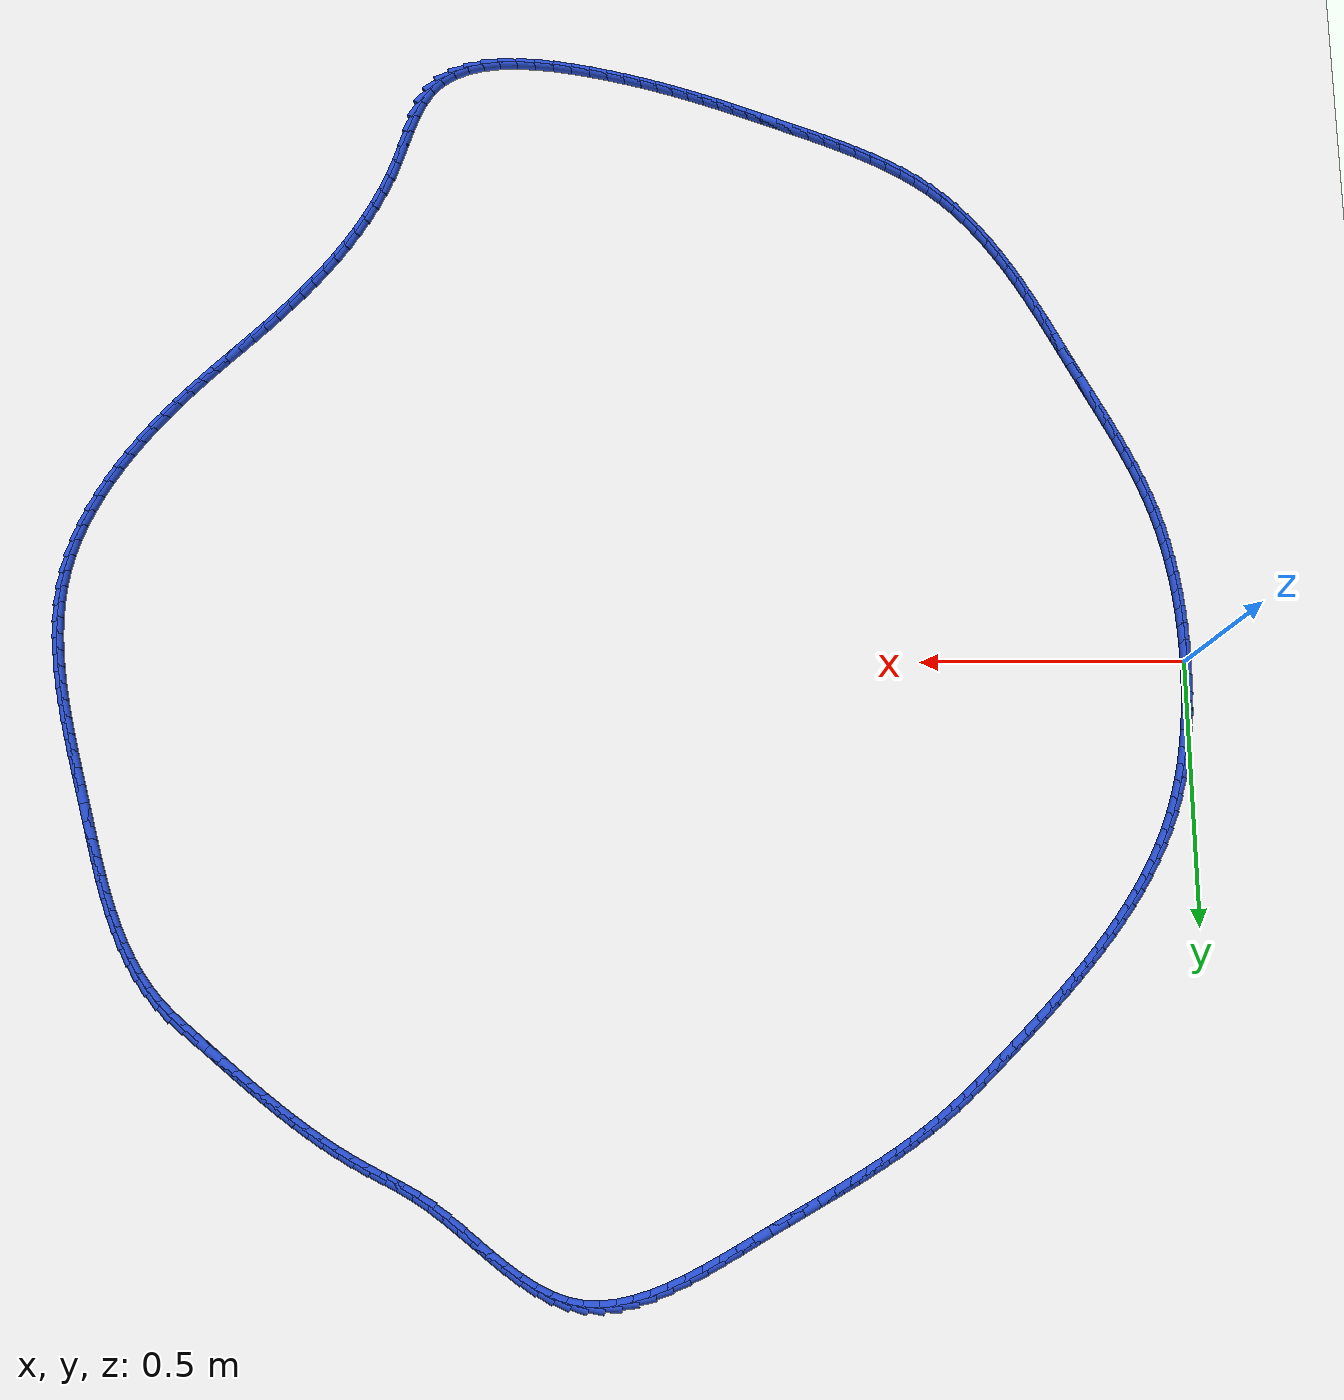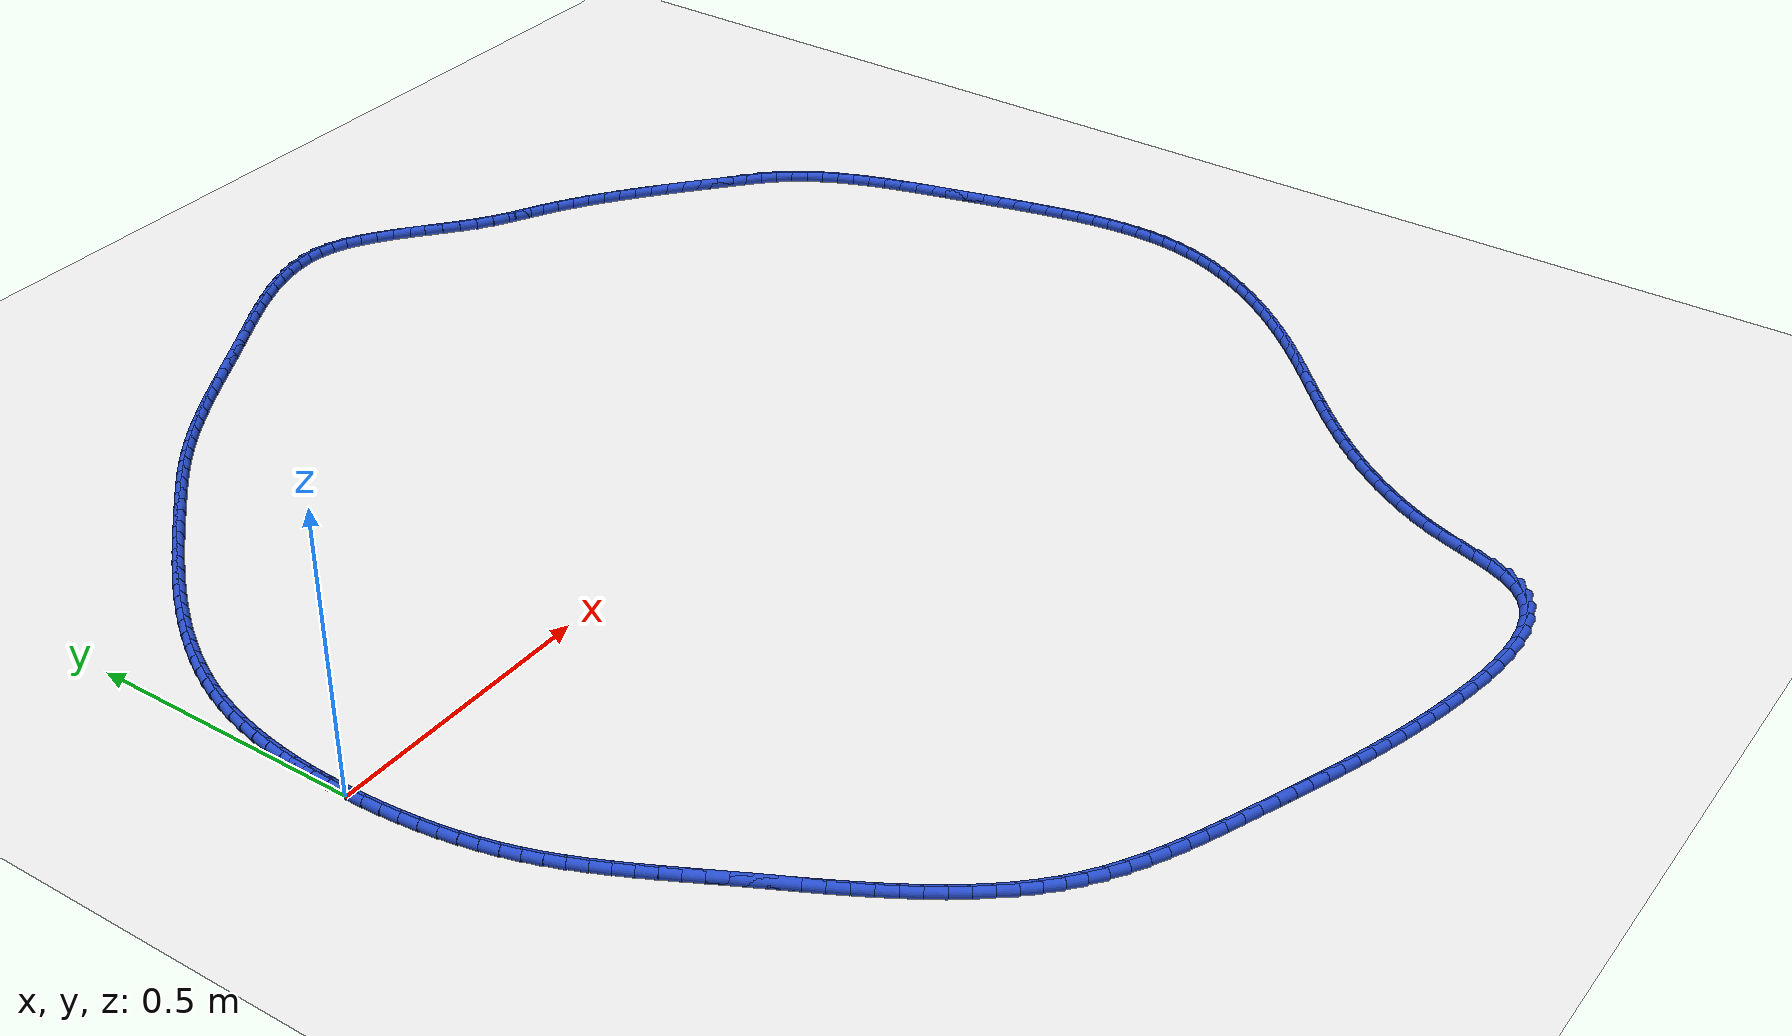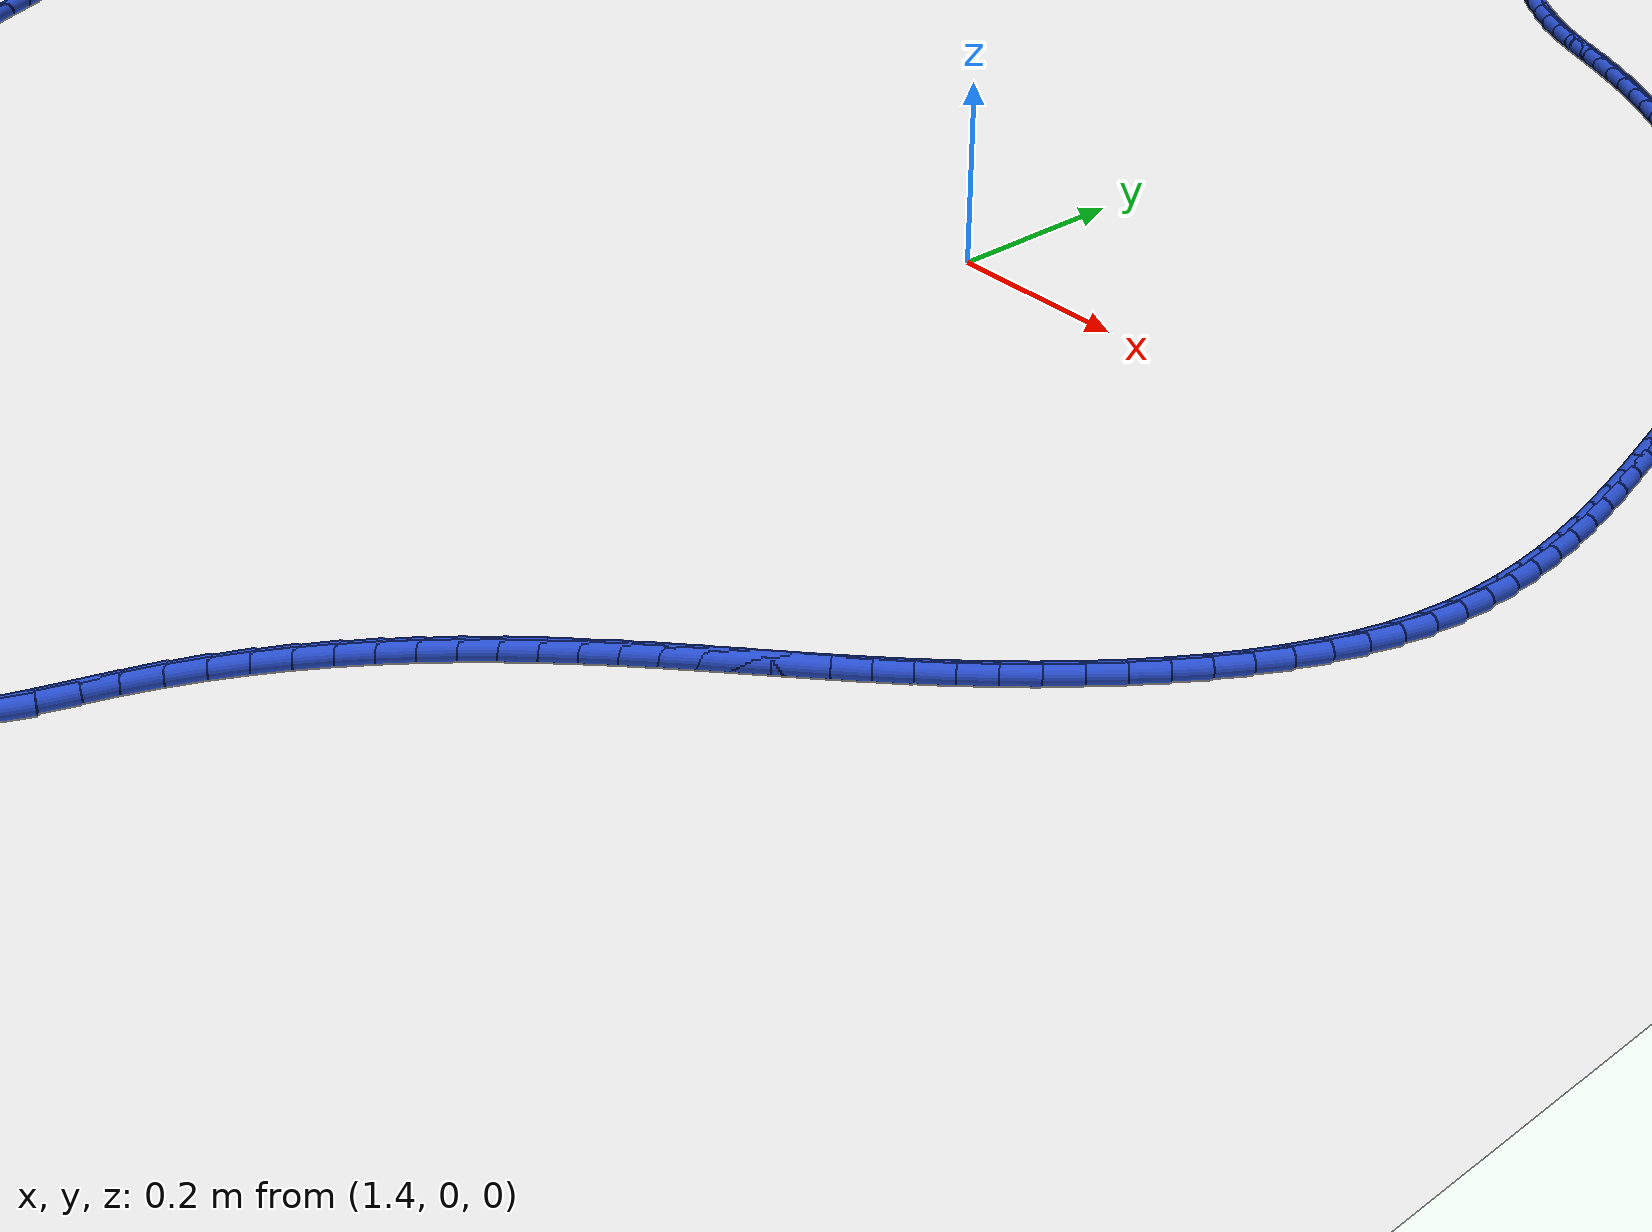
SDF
<sdf version="1.6">
 <world name="default">
  <light name="sun" type="directional">
   <pose>0 0 10 0 -0 0</pose>
   <diffuse>0.8 0.8 0.8 1</diffuse>
   <specular>0.2 0.2 0.2 1</specular>
   <attenuation>
    <range>1000</range>
    <constant>0.9</constant>
    <linear>0.01</linear>
    <quadratic>0.001</quadratic>
   </attenuation>
   <direction>-0.5 0.1 -0.9</direction>
  </light>
  <model name="ground_plane">
   <static>1</static>
   <link name="link">
    <collision name="collision">
     <geometry><plane><normal>0 0 1</normal><size>100 100</size></plane></geometry>
     <surface><friction><ode><mu>100</mu><mu2>50</mu2></ode></friction></surface>
    </collision>
    <visual name="visual">
     <cast_shadows>0</cast_shadows>
     <geometry><plane><normal>0 0 1</normal><size>100 100</size></plane></geometry>
     <material>
      <script><uri>file://media/materials/scripts/gazebo.material</uri><name>Gazebo/WhiteGlow</name></script>
     </material>
    </visual>
   </link>
  </model>
  <gravity>0 0 -9.8</gravity>
  <magnetic_field>6e-06 2.3e-05 -4.2e-05</magnetic_field>
  <atmosphere type="adiabatic"/>
  <physics name="default_physics" default="0" type="ode">
   <max_step_size>0.001</max_step_size>
   <real_time_factor>1</real_time_factor>
   <real_time_update_rate>1000</real_time_update_rate>
  </physics>
  <scene><ambient>0.4 0.4 0.4 1</ambient><background>0.7 0.7 0.7 1</background><shadows>1</shadows></scene>
  <spherical_coordinates>
   <surface_model>EARTH_WGS84</surface_model>
   <latitude_deg>0</latitude_deg>
   <longitude_deg>0</longitude_deg>
   <elevation>0</elevation>
   <heading_deg>0</heading_deg>
  </spherical_coordinates>
  <model name="line">
   <link name="link_0">
    <pose>1.214306433183765e-17 -6.938893903907228e-17 0.01 0 1.57 1.5625479903937716</pose>
    <collision name="collision">
     <geometry><cylinder><radius>0.01</radius><length>0.08</length></cylinder></geometry>
    </collision>
    <visual name="visual">
     <material>
      <script><name>Gazebo/Blue</name><uri>file://media/materials/scripts/gazebo.material</uri></script>
     </material>
     <geometry><cylinder><radius>0.01</radius><length>0.08</length></cylinder></geometry>
    </visual>
   </link>
   <link name="link_1">
    <pose>0.00027351978538002117 0.03315984812850653 0.01 0 1.57 1.5339640147041222</pose>
    <collision name="collision">
     <geometry><cylinder><radius>0.01</radius><length>0.08</length></cylinder></geometry>
    </collision>
    <visual name="visual">
     <material>
      <script><name>Gazebo/Blue</name><uri>file://media/materials/scripts/gazebo.material</uri></script>
     </material>
     <geometry><cylinder><radius>0.01</radius><length>0.08</length></cylinder></geometry>
    </visual>
   </link>
   <link name="link_2">
    <pose>0.001493885571331773 0.06627788524233025 0.01 0 1.57 1.502925482752738</pose>
    <collision name="collision">
     <geometry><cylinder><radius>0.01</radius><length>0.08</length></cylinder></geometry>
    </collision>
    <visual name="visual">
     <material>
      <script><name>Gazebo/Blue</name><uri>file://media/materials/scripts/gazebo.material</uri></script>
     </material>
     <geometry><cylinder><radius>0.01</radius><length>0.08</length></cylinder></geometry>
    </visual>
   </link>
   <link name="link_3">
    <pose>0.0037371043291328397 0.0992784071167581 0.01 0 1.57 1.4692765700750796</pose>
    <collision name="collision">
     <geometry><cylinder><radius>0.01</radius><length>0.08</length></cylinder></geometry>
    </collision>
    <visual name="visual">
     <material>
      <script><name>Gazebo/Blue</name><uri>file://media/materials/scripts/gazebo.material</uri></script>
     </material>
     <geometry><cylinder><radius>0.01</radius><length>0.08</length></cylinder></geometry>
    </visual>
   </link>
   <link name="link_4">
    <pose>0.007079183030060788 0.13208570952707716 0.01 0 1.57 1.4328588573764192</pose>
    <collision name="collision">
     <geometry><cylinder><radius>0.01</radius><length>0.08</length></cylinder></geometry>
    </collision>
    <visual name="visual">
     <material>
      <script><name>Gazebo/Blue</name><uri>file://media/materials/scripts/gazebo.material</uri></script>
     </material>
     <geometry><cylinder><radius>0.01</radius><length>0.08</length></cylinder></geometry>
    </visual>
   </link>
   <link name="link_5">
    <pose>0.011596128645393196 0.16462408824857458 0.01 0 1.57 1.3935175337363084</pose>
    <collision name="collision">
     <geometry><cylinder><radius>0.01</radius><length>0.08</length></cylinder></geometry>
    </collision>
    <visual name="visual">
     <material>
      <script><name>Gazebo/Blue</name><uri>file://media/materials/scripts/gazebo.material</uri></script>
     </material>
     <geometry><cylinder><radius>0.01</radius><length>0.08</length></cylinder></geometry>
    </visual>
   </link>
   <link name="link_6">
    <pose>0.017363948146407633 0.19681783905653732 0.01 0 1.57 1.3511096710920563</pose>
    <collision name="collision">
     <geometry><cylinder><radius>0.01</radius><length>0.08</length></cylinder></geometry>
    </collision>
    <visual name="visual">
     <material>
      <script><name>Gazebo/Blue</name><uri>file://media/materials/scripts/gazebo.material</uri></script>
     </material>
     <geometry><cylinder><radius>0.01</radius><length>0.08</length></cylinder></geometry>
    </visual>
   </link>
   <link name="link_7">
    <pose>0.024458648504381664 0.22859125772625244 0.01 0 1.57 1.3055148705598156</pose>
    <collision name="collision">
     <geometry><cylinder><radius>0.01</radius><length>0.08</length></cylinder></geometry>
    </collision>
    <visual name="visual">
     <material>
      <script><name>Gazebo/Blue</name><uri>file://media/materials/scripts/gazebo.material</uri></script>
     </material>
     <geometry><cylinder><radius>0.01</radius><length>0.08</length></cylinder></geometry>
    </visual>
   </link>
   <link name="link_8">
    <pose>0.032956236690592854 0.25986864003300697 0.01 0 1.57 1.2566483965181106</pose>
    <collision name="collision">
     <geometry><cylinder><radius>0.01</radius><length>0.08</length></cylinder></geometry>
    </collision>
    <visual name="visual">
     <material>
      <script><name>Gazebo/Blue</name><uri>file://media/materials/scripts/gazebo.material</uri></script>
     </material>
     <geometry><cylinder><radius>0.01</radius><length>0.08</length></cylinder></geometry>
    </visual>
   </link>
   <link name="link_9">
    <pose>0.04293271967631879 0.2905742817520881 0.01 0 1.57 1.205137989634561</pose>
    <collision name="collision">
     <geometry><cylinder><radius>0.01</radius><length>0.08</length></cylinder></geometry>
    </collision>
    <visual name="visual">
     <material>
      <script><name>Gazebo/Blue</name><uri>file://media/materials/scripts/gazebo.material</uri></script>
     </material>
     <geometry><cylinder><radius>0.01</radius><length>0.08</length></cylinder></geometry>
    </visual>
   </link>
   <link name="link_10">
    <pose>0.05444557960911423 0.320643647442514 0.01 0 1.57 1.1550896922501135</pose>
    <collision name="collision">
     <geometry><cylinder><radius>0.01</radius><length>0.08</length></cylinder></geometry>
    </collision>
    <visual name="visual">
     <material>
      <script><name>Gazebo/Blue</name><uri>file://media/materials/scripts/gazebo.material</uri></script>
     </material>
     <geometry><cylinder><radius>0.01</radius><length>0.08</length></cylinder></geometry>
    </visual>
   </link>
   <link name="link_11">
    <pose>0.06743977099053443 0.35008004559859457 0.01 0 1.57 1.1082006075892776</pose>
    <collision name="collision">
     <geometry><cylinder><radius>0.01</radius><length>0.08</length></cylinder></geometry>
    </collision>
    <visual name="visual">
     <material>
      <script><name>Gazebo/Blue</name><uri>file://media/materials/scripts/gazebo.material</uri></script>
     </material>
     <geometry><cylinder><radius>0.01</radius><length>0.08</length></cylinder></geometry>
    </visual>
   </link>
   <link name="link_12">
    <pose>0.08181798925542157 0.3789122630880841 0.01 0 1.57 1.0646013945800745</pose>
    <collision name="collision">
     <geometry><cylinder><radius>0.01</radius><length>0.08</length></cylinder></geometry>
    </collision>
    <visual name="visual">
     <material>
      <script><name>Gazebo/Blue</name><uri>file://media/materials/scripts/gazebo.material</uri></script>
     </material>
     <geometry><cylinder><radius>0.01</radius><length>0.08</length></cylinder></geometry>
    </visual>
   </link>
   <link name="link_13">
    <pose>0.09748285429300632 0.40716913232586904 0.01 0 1.57 1.0243509187423478</pose>
    <collision name="collision">
     <geometry><cylinder><radius>0.01</radius><length>0.08</length></cylinder></geometry>
    </collision>
    <visual name="visual">
     <material>
      <script><name>Gazebo/Blue</name><uri>file://media/materials/scripts/gazebo.material</uri></script>
     </material>
     <geometry><cylinder><radius>0.01</radius><length>0.08</length></cylinder></geometry>
    </visual>
   </link>
   <link name="link_14">
    <pose>0.11433698599251936 0.43487948572683605 0.01 0 1.57 0.9874526236476397</pose>
    <collision name="collision">
     <geometry><cylinder><radius>0.01</radius><length>0.08</length></cylinder></geometry>
    </collision>
    <visual name="visual">
     <material>
      <script><name>Gazebo/Blue</name><uri>file://media/materials/scripts/gazebo.material</uri></script>
     </material>
     <geometry><cylinder><radius>0.01</radius><length>0.08</length></cylinder></geometry>
    </visual>
   </link>
   <link name="link_15">
    <pose>0.1322830042431913 0.46207215570587157 0.01 0 1.57 0.9538682935010617</pose>
    <collision name="collision">
     <geometry><cylinder><radius>0.01</radius><length>0.08</length></cylinder></geometry>
    </collision>
    <visual name="visual">
     <material>
      <script><name>Gazebo/Blue</name><uri>file://media/materials/scripts/gazebo.material</uri></script>
     </material>
     <geometry><cylinder><radius>0.01</radius><length>0.08</length></cylinder></geometry>
    </visual>
   </link>
   <link name="link_16">
    <pose>0.15122352893425275 0.48877597467786177 0.01 0 1.57 0.9235308130817051</pose>
    <collision name="collision">
     <geometry><cylinder><radius>0.01</radius><length>0.08</length></cylinder></geometry>
    </collision>
    <visual name="visual">
     <material>
      <script><name>Gazebo/Blue</name><uri>file://media/materials/scripts/gazebo.material</uri></script>
     </material>
     <geometry><cylinder><radius>0.01</radius><length>0.08</length></cylinder></geometry>
    </visual>
   </link>
   <link name="link_17">
    <pose>0.17106117995493442 0.5150197750576937 0.01 0 1.57 0.8963553222531527</pose>
    <collision name="collision">
     <geometry><cylinder><radius>0.01</radius><length>0.08</length></cylinder></geometry>
    </collision>
    <visual name="visual">
     <material>
      <script><name>Gazebo/Blue</name><uri>file://media/materials/scripts/gazebo.material</uri></script>
     </material>
     <geometry><cylinder><radius>0.01</radius><length>0.08</length></cylinder></geometry>
    </visual>
   </link>
   <link name="link_18">
    <pose>0.19169857719446703 0.5408323892602536 0.01 0 1.57 0.872248544255945</pose>
    <collision name="collision">
     <geometry><cylinder><radius>0.01</radius><length>0.08</length></cylinder></geometry>
    </collision>
    <visual name="visual">
     <material>
      <script><name>Gazebo/Blue</name><uri>file://media/materials/scripts/gazebo.material</uri></script>
     </material>
     <geometry><cylinder><radius>0.01</radius><length>0.08</length></cylinder></geometry>
    </visual>
   </link>
   <link name="link_19">
    <pose>0.21303834054208118 0.566242649700428 0.01 0 1.57 0.8511163273038134</pose>
    <collision name="collision">
     <geometry><cylinder><radius>0.01</radius><length>0.08</length></cylinder></geometry>
    </collision>
    <visual name="visual">
     <material>
      <script><name>Gazebo/Blue</name><uri>file://media/materials/scripts/gazebo.material</uri></script>
     </material>
     <geometry><cylinder><radius>0.01</radius><length>0.08</length></cylinder></geometry>
    </visual>
   </link>
   <link name="link_20">
    <pose>0.2349830898870074 0.5912793887931036 0.01 0 1.57 0.8328695917835235</pose>
    <collision name="collision">
     <geometry><cylinder><radius>0.01</radius><length>0.08</length></cylinder></geometry>
    </collision>
    <visual name="visual">
     <material>
      <script><name>Gazebo/Blue</name><uri>file://media/materials/scripts/gazebo.material</uri></script>
     </material>
     <geometry><cylinder><radius>0.01</radius><length>0.08</length></cylinder></geometry>
    </visual>
   </link>
   <link name="link_21">
    <pose>0.2574354451184765 0.6159714389531667 0.01 0 1.57 0.8174289467947158</pose>
    <collision name="collision">
     <geometry><cylinder><radius>0.01</radius><length>0.08</length></cylinder></geometry>
    </collision>
    <visual name="visual">
     <material>
      <script><name>Gazebo/Blue</name><uri>file://media/materials/scripts/gazebo.material</uri></script>
     </material>
     <geometry><cylinder><radius>0.01</radius><length>0.08</length></cylinder></geometry>
    </visual>
   </link>
   <link name="link_22">
    <pose>0.2802980261257191 0.640347632595504 0.01 0 1.57 0.8047282567486036</pose>
    <collision name="collision">
     <geometry><cylinder><radius>0.01</radius><length>0.08</length></cylinder></geometry>
    </collision>
    <visual name="visual">
     <material>
      <script><name>Gazebo/Blue</name><uri>file://media/materials/scripts/gazebo.material</uri></script>
     </material>
     <geometry><cylinder><radius>0.01</radius><length>0.08</length></cylinder></geometry>
    </visual>
   </link>
   <link name="link_23">
    <pose>0.30347345279796584 0.6644368021350018 0.01 0 1.57 0.7947174233926166</pose>
    <collision name="collision">
     <geometry><cylinder><radius>0.01</radius><length>0.08</length></cylinder></geometry>
    </collision>
    <visual name="visual">
     <material>
      <script><name>Gazebo/Blue</name><uri>file://media/materials/scripts/gazebo.material</uri></script>
     </material>
     <geometry><cylinder><radius>0.01</radius><length>0.08</length></cylinder></geometry>
    </visual>
   </link>
   <link name="link_24">
    <pose>0.32686434502444706 0.6882677799865464 0.01 0 1.57 0.787364616732721</pose>
    <collision name="collision">
     <geometry><cylinder><radius>0.01</radius><length>0.08</length></cylinder></geometry>
    </collision>
    <visual name="visual">
     <material>
      <script><name>Gazebo/Blue</name><uri>file://media/materials/scripts/gazebo.material</uri></script>
     </material>
     <geometry><cylinder><radius>0.01</radius><length>0.08</length></cylinder></geometry>
    </visual>
   </link>
   <link name="link_25">
    <pose>0.35037332269439414 0.7118693985650252 0.01 0 1.57 0.7826398959665777</pose>
    <collision name="collision">
     <geometry><cylinder><radius>0.01</radius><length>0.08</length></cylinder></geometry>
    </collision>
    <visual name="visual">
     <material>
      <script><name>Gazebo/Blue</name><uri>file://media/materials/scripts/gazebo.material</uri></script>
     </material>
     <geometry><cylinder><radius>0.01</radius><length>0.08</length></cylinder></geometry>
    </visual>
   </link>
   <link name="link_26">
    <pose>0.37390343516154334 0.7352700630702641 0.01 0 1.57 0.7776863904397144</pose>
    <collision name="collision">
     <geometry><cylinder><radius>0.01</radius><length>0.08</length></cylinder></geometry>
    </collision>
    <visual name="visual">
     <material>
      <script><name>Gazebo/Blue</name><uri>file://media/materials/scripts/gazebo.material</uri></script>
     </material>
     <geometry><cylinder><radius>0.01</radius><length>0.08</length></cylinder></geometry>
    </visual>
   </link>
   <link name="link_27">
    <pose>0.39742482399979673 0.7584314378972128 0.01 0 1.57 0.7664854347598168</pose>
    <collision name="collision">
     <geometry><cylinder><radius>0.01</radius><length>0.08</length></cylinder></geometry>
    </collision>
    <visual name="visual">
     <material>
      <script><name>Gazebo/Blue</name><uri>file://media/materials/scripts/gazebo.material</uri></script>
     </material>
     <geometry><cylinder><radius>0.01</radius><length>0.08</length></cylinder></geometry>
    </visual>
   </link>
   <link name="link_28">
    <pose>0.4210469853556649 0.7811765627788734 0.01 0 1.57 0.7481174663807753</pose>
    <collision name="collision">
     <geometry><cylinder><radius>0.01</radius><length>0.08</length></cylinder></geometry>
    </collision>
    <visual name="visual">
     <material>
      <script><name>Gazebo/Blue</name><uri>file://media/materials/scripts/gazebo.material</uri></script>
     </material>
     <geometry><cylinder><radius>0.01</radius><length>0.08</length></cylinder></geometry>
    </visual>
   </link>
   <link name="link_29">
    <pose>0.44489676637751224 0.8033112173273844 0.01 0 1.57 0.7223581899397177</pose>
    <collision name="collision">
     <geometry><cylinder><radius>0.01</radius><length>0.08</length></cylinder></geometry>
    </collision>
    <visual name="visual">
     <material>
      <script><name>Gazebo/Blue</name><uri>file://media/materials/scripts/gazebo.material</uri></script>
     </material>
     <geometry><cylinder><radius>0.01</radius><length>0.08</length></cylinder></geometry>
    </visual>
   </link>
   <link name="link_30">
    <pose>0.46910101421370337 0.8246411811548838 0.01 0 1.57 0.6894745957663395</pose>
    <collision name="collision">
     <geometry><cylinder><radius>0.01</radius><length>0.08</length></cylinder></geometry>
    </collision>
    <visual name="visual">
     <material>
      <script><name>Gazebo/Blue</name><uri>file://media/materials/scripts/gazebo.material</uri></script>
     </material>
     <geometry><cylinder><radius>0.01</radius><length>0.08</length></cylinder></geometry>
    </visual>
   </link>
   <link name="link_31">
    <pose>0.4937802443783938 0.8449880511693444 0.01 0 1.57 0.6554341247298708</pose>
    <collision name="collision">
     <geometry><cylinder><radius>0.01</radius><length>0.08</length></cylinder></geometry>
    </collision>
    <visual name="visual">
     <material>
      <script><name>Gazebo/Blue</name><uri>file://media/materials/scripts/gazebo.material</uri></script>
     </material>
     <geometry><cylinder><radius>0.01</radius><length>0.08</length></cylinder></geometry>
    </visual>
   </link>
   <link name="link_32">
    <pose>0.5189796094254182 0.8643616913515374 0.01 0 1.57 0.6245075182410981</pose>
    <collision name="collision">
     <geometry><cylinder><radius>0.01</radius><length>0.08</length></cylinder></geometry>
    </collision>
    <visual name="visual">
     <material>
      <script><name>Gazebo/Blue</name><uri>file://media/materials/scripts/gazebo.material</uri></script>
     </material>
     <geometry><cylinder><radius>0.01</radius><length>0.08</length></cylinder></geometry>
    </visual>
   </link>
   <link name="link_33">
    <pose>0.5446947927871263 0.8828955463730126 0.01 0 1.57 0.5970752957010125</pose>
    <collision name="collision">
     <geometry><cylinder><radius>0.01</radius><length>0.08</length></cylinder></geometry>
    </collision>
    <visual name="visual">
     <material>
      <script><name>Gazebo/Blue</name><uri>file://media/materials/scripts/gazebo.material</uri></script>
     </material>
     <geometry><cylinder><radius>0.01</radius><length>0.08</length></cylinder></geometry>
    </visual>
   </link>
   <link name="link_34">
    <pose>0.5709206144676275 0.9007252178681924 0.01 0 1.57 0.5733649681810913</pose>
    <collision name="collision">
     <geometry><cylinder><radius>0.01</radius><length>0.08</length></cylinder></geometry>
    </collision>
    <visual name="visual">
     <material>
      <script><name>Gazebo/Blue</name><uri>file://media/materials/scripts/gazebo.material</uri></script>
     </material>
     <geometry><cylinder><radius>0.01</radius><length>0.08</length></cylinder></geometry>
    </visual>
   </link>
   <link name="link_35">
    <pose>0.5976518944710318 0.9179863074714997 0.01 0 1.57 0.5535233577818326</pose>
    <collision name="collision">
     <geometry><cylinder><radius>0.01</radius><length>0.08</length></cylinder></geometry>
    </collision>
    <visual name="visual">
     <material>
      <script><name>Gazebo/Blue</name><uri>file://media/materials/scripts/gazebo.material</uri></script>
     </material>
     <geometry><cylinder><radius>0.01</radius><length>0.08</length></cylinder></geometry>
    </visual>
   </link>
   <link name="link_36">
    <pose>0.624883452801448 0.9348144168173574 0.01 0 1.57 0.537623305985912</pose>
    <collision name="collision">
     <geometry><cylinder><radius>0.01</radius><length>0.08</length></cylinder></geometry>
    </collision>
    <visual name="visual">
     <material>
      <script><name>Gazebo/Blue</name><uri>file://media/materials/scripts/gazebo.material</uri></script>
     </material>
     <geometry><cylinder><radius>0.01</radius><length>0.08</length></cylinder></geometry>
    </visual>
   </link>
   <link name="link_37">
    <pose>0.6526101094629863 0.9513451475401883 0.01 0 1.57 0.5256723691486967</pose>
    <collision name="collision">
     <geometry><cylinder><radius>0.01</radius><length>0.08</length></cylinder></geometry>
    </collision>
    <visual name="visual">
     <material>
      <script><name>Gazebo/Blue</name><uri>file://media/materials/scripts/gazebo.material</uri></script>
     </material>
     <geometry><cylinder><radius>0.01</radius><length>0.08</length></cylinder></geometry>
    </visual>
   </link>
   <link name="link_38">
    <pose>0.6808266844597556 0.9677141012744147 0.01 0 1.57 0.5176221398500229</pose>
    <collision name="collision">
     <geometry><cylinder><radius>0.01</radius><length>0.08</length></cylinder></geometry>
    </collision>
    <visual name="visual">
     <material>
      <script><name>Gazebo/Blue</name><uri>file://media/materials/scripts/gazebo.material</uri></script>
     </material>
     <geometry><cylinder><radius>0.01</radius><length>0.08</length></cylinder></geometry>
    </visual>
   </link>
   <link name="link_39">
    <pose>0.7095279977958657 0.9840568796544595 0.01 0 1.57 0.5133772083083311</pose>
    <collision name="collision">
     <geometry><cylinder><radius>0.01</radius><length>0.08</length></cylinder></geometry>
    </collision>
    <visual name="visual">
     <material>
      <script><name>Gazebo/Blue</name><uri>file://media/materials/scripts/gazebo.material</uri></script>
     </material>
     <geometry><cylinder><radius>0.01</radius><length>0.08</length></cylinder></geometry>
    </visual>
   </link>
   <link name="link_40">
    <pose>0.7387088694754264 1.0005090843147462 0.01 0 1.57 0.5128031732810909</pose>
    <collision name="collision">
     <geometry><cylinder><radius>0.01</radius><length>0.08</length></cylinder></geometry>
    </collision>
    <visual name="visual">
     <material>
      <script><name>Gazebo/Blue</name><uri>file://media/materials/scripts/gazebo.material</uri></script>
     </material>
     <geometry><cylinder><radius>0.01</radius><length>0.08</length></cylinder></geometry>
    </visual>
   </link>
   <link name="link_41">
    <pose>0.7683641195025468 1.0172063168896963 0.01 0 1.57 0.5157334553198087</pose>
    <collision name="collision">
     <geometry><cylinder><radius>0.01</radius><length>0.08</length></cylinder></geometry>
    </collision>
    <visual name="visual">
     <material>
      <script><name>Gazebo/Blue</name><uri>file://media/materials/scripts/gazebo.material</uri></script>
     </material>
     <geometry><cylinder><radius>0.01</radius><length>0.08</length></cylinder></geometry>
    </visual>
   </link>
   <link name="link_42">
    <pose>0.7984885678813362 1.034284179013733 0.01 0 1.57 0.5212183942930964</pose>
    <collision name="collision">
     <geometry><cylinder><radius>0.01</radius><length>0.08</length></cylinder></geometry>
    </collision>
    <visual name="visual">
     <material>
      <script><name>Gazebo/Blue</name><uri>file://media/materials/scripts/gazebo.material</uri></script>
     </material>
     <geometry><cylinder><radius>0.01</radius><length>0.08</length></cylinder></geometry>
    </visual>
   </link>
   <link name="link_43">
    <pose>0.8290711453369805 1.051844107110256 0.01 0 1.57 0.5213794743828627</pose>
    <collision name="collision">
     <geometry><cylinder><radius>0.01</radius><length>0.08</length></cylinder></geometry>
    </collision>
    <visual name="visual">
     <material>
      <script><name>Gazebo/Blue</name><uri>file://media/materials/scripts/gazebo.material</uri></script>
     </material>
     <geometry><cylinder><radius>0.01</radius><length>0.08</length></cylinder></geometry>
    </visual>
   </link>
   <link name="link_44">
    <pose>0.860039529277675 1.069632191468146 0.01 0 1.57 0.5118029143572922</pose>
    <collision name="collision">
     <geometry><cylinder><radius>0.01</radius><length>0.08</length></cylinder></geometry>
    </collision>
    <visual name="visual">
     <material>
      <script><name>Gazebo/Blue</name><uri>file://media/materials/scripts/gazebo.material</uri></script>
     </material>
     <geometry><cylinder><radius>0.01</radius><length>0.08</length></cylinder></geometry>
    </visual>
   </link>
   <link name="link_45">
    <pose>0.8912850529848453 1.087183680815452 0.01 0 1.57 0.4922716023065845</pose>
    <collision name="collision">
     <geometry><cylinder><radius>0.01</radius><length>0.08</length></cylinder></geometry>
    </collision>
    <visual name="visual">
     <material>
      <script><name>Gazebo/Blue</name><uri>file://media/materials/scripts/gazebo.material</uri></script>
     </material>
     <geometry><cylinder><radius>0.01</radius><length>0.08</length></cylinder></geometry>
    </visual>
   </link>
   <link name="link_46">
    <pose>0.9226985718743982 1.1040310516603098 0.01 0 1.57 0.462109692796905</pose>
    <collision name="collision">
     <geometry><cylinder><radius>0.01</radius><length>0.08</length></cylinder></geometry>
    </collision>
    <visual name="visual">
     <material>
      <script><name>Gazebo/Blue</name><uri>file://media/materials/scripts/gazebo.material</uri></script>
     </material>
     <geometry><cylinder><radius>0.01</radius><length>0.08</length></cylinder></geometry>
    </visual>
   </link>
   <link name="link_47">
    <pose>0.954170941362239 1.119706780510853 0.01 0 1.57 0.4201148063069758</pose>
    <collision name="collision">
     <geometry><cylinder><radius>0.01</radius><length>0.08</length></cylinder></geometry>
    </collision>
    <visual name="visual">
     <material>
      <script><name>Gazebo/Blue</name><uri>file://media/materials/scripts/gazebo.material</uri></script>
     </material>
     <geometry><cylinder><radius>0.01</radius><length>0.08</length></cylinder></geometry>
    </visual>
   </link>
   <link name="link_48">
    <pose>0.9855930168642739 1.1337433438752158 0.01 0 1.57 0.36454583480245956</pose>
    <collision name="collision">
     <geometry><cylinder><radius>0.01</radius><length>0.08</length></cylinder></geometry>
    </collision>
    <visual name="visual">
     <material>
      <script><name>Gazebo/Blue</name><uri>file://media/materials/scripts/gazebo.material</uri></script>
     </material>
     <geometry><cylinder><radius>0.01</radius><length>0.08</length></cylinder></geometry>
    </visual>
   </link>
   <link name="link_49">
    <pose>1.0168556537964093 1.145673218261533 0.01 0 1.57 0.29315633438910066</pose>
    <collision name="collision">
     <geometry><cylinder><radius>0.01</radius><length>0.08</length></cylinder></geometry>
    </collision>
    <visual name="visual">
     <material>
      <script><name>Gazebo/Blue</name><uri>file://media/materials/scripts/gazebo.material</uri></script>
     </material>
     <geometry><cylinder><radius>0.01</radius><length>0.08</length></cylinder></geometry>
    </visual>
   </link>
   <link name="link_50">
    <pose>1.0478497075745508 1.1550288801779387 0.01 0 1.57 0.2033762307669449</pose>
    <collision name="collision">
     <geometry><cylinder><radius>0.01</radius><length>0.08</length></cylinder></geometry>
    </collision>
    <visual name="visual">
     <material>
      <script><name>Gazebo/Blue</name><uri>file://media/materials/scripts/gazebo.material</uri></script>
     </material>
     <geometry><cylinder><radius>0.01</radius><length>0.08</length></cylinder></geometry>
    </visual>
   </link>
   <link name="link_51">
    <pose>1.078466033614605 1.1613428061325675 0.01 0 1.57 0.09281971597217803</pose>
    <collision name="collision">
     <geometry><cylinder><radius>0.01</radius><length>0.08</length></cylinder></geometry>
    </collision>
    <visual name="visual">
     <material>
      <script><name>Gazebo/Blue</name><uri>file://media/materials/scripts/gazebo.material</uri></script>
     </material>
     <geometry><cylinder><radius>0.01</radius><length>0.08</length></cylinder></geometry>
    </visual>
   </link>
   <link name="link_52">
    <pose>1.108595487332477 1.1641474726335532 0.01 0 1.57 -0.03966695867732513</pose>
    <collision name="collision">
     <geometry><cylinder><radius>0.01</radius><length>0.08</length></cylinder></geometry>
    </collision>
    <visual name="visual">
     <material>
      <script><name>Gazebo/Blue</name><uri>file://media/materials/scripts/gazebo.material</uri></script>
     </material>
     <geometry><cylinder><radius>0.01</radius><length>0.08</length></cylinder></geometry>
    </visual>
   </link>
   <link name="link_53">
    <pose>1.1381289241440744 1.1629753561890308 0.01 0 1.57 -0.1917910922669778</pose>
    <collision name="collision">
     <geometry><cylinder><radius>0.01</radius><length>0.08</length></cylinder></geometry>
    </collision>
    <visual name="visual">
     <material>
      <script><name>Gazebo/Blue</name><uri>file://media/materials/scripts/gazebo.material</uri></script>
     </material>
     <geometry><cylinder><radius>0.01</radius><length>0.08</length></cylinder></geometry>
    </visual>
   </link>
   <link name="link_54">
    <pose>1.166961019299047 1.1573768028403908 0.01 0 1.57 -0.34009776362689115</pose>
    <collision name="collision">
     <geometry><cylinder><radius>0.01</radius><length>0.08</length></cylinder></geometry>
    </collision>
    <visual name="visual">
     <material>
      <script><name>Gazebo/Blue</name><uri>file://media/materials/scripts/gazebo.material</uri></script>
     </material>
     <geometry><cylinder><radius>0.01</radius><length>0.08</length></cylinder></geometry>
    </visual>
   </link>
   <link name="link_55">
    <pose>1.1950973265280922 1.1474208583517393 0.01 0 1.57 -0.4599225659053167</pose>
    <collision name="collision">
     <geometry><cylinder><radius>0.01</radius><length>0.08</length></cylinder></geometry>
    </collision>
    <visual name="visual">
     <material>
      <script><name>Gazebo/Blue</name><uri>file://media/materials/scripts/gazebo.material</uri></script>
     </material>
     <geometry><cylinder><radius>0.01</radius><length>0.08</length></cylinder></geometry>
    </visual>
   </link>
   <link name="link_56">
    <pose>1.2226688118757438 1.1337632588151705 0.01 0 1.57 -0.5507930033713385</pose>
    <collision name="collision">
     <geometry><cylinder><radius>0.01</radius><length>0.08</length></cylinder></geometry>
    </collision>
    <visual name="visual">
     <material>
      <script><name>Gazebo/Blue</name><uri>file://media/materials/scripts/gazebo.material</uri></script>
     </material>
     <geometry><cylinder><radius>0.01</radius><length>0.08</length></cylinder></geometry>
    </visual>
   </link>
   <link name="link_57">
    <pose>1.2498131818181022 1.1170912726810192 0.01 0 1.57 -0.6157224338253602</pose>
    <collision name="collision">
     <geometry><cylinder><radius>0.01</radius><length>0.08</length></cylinder></geometry>
    </collision>
    <visual name="visual">
     <material>
      <script><name>Gazebo/Blue</name><uri>file://media/materials/scripts/gazebo.material</uri></script>
     </material>
     <geometry><cylinder><radius>0.01</radius><length>0.08</length></cylinder></geometry>
    </visual>
   </link>
   <link name="link_58">
    <pose>1.276668142831268 1.09809216839962 0.01 0 1.57 -0.657996873678657</pose>
    <collision name="collision">
     <geometry><cylinder><radius>0.01</radius><length>0.08</length></cylinder></geometry>
    </collision>
    <visual name="visual">
     <material>
      <script><name>Gazebo/Blue</name><uri>file://media/materials/scripts/gazebo.material</uri></script>
     </material>
     <geometry><cylinder><radius>0.01</radius><length>0.08</length></cylinder></geometry>
    </visual>
   </link>
   <link name="link_59">
    <pose>1.303371401391344 1.0774532144213087 0.01 0 1.57 -0.680202934170221</pose>
    <collision name="collision">
     <geometry><cylinder><radius>0.01</radius><length>0.08</length></cylinder></geometry>
    </collision>
    <visual name="visual">
     <material>
      <script><name>Gazebo/Blue</name><uri>file://media/materials/scripts/gazebo.material</uri></script>
     </material>
     <geometry><cylinder><radius>0.01</radius><length>0.08</length></cylinder></geometry>
    </visual>
   </link>
   <link name="link_60">
    <pose>1.3300606639744306 1.0558616791964186 0.01 0 1.57 -0.6839163904575002</pose>
    <collision name="collision">
     <geometry><cylinder><radius>0.01</radius><length>0.08</length></cylinder></geometry>
    </collision>
    <visual name="visual">
     <material>
      <script><name>Gazebo/Blue</name><uri>file://media/materials/scripts/gazebo.material</uri></script>
     </material>
     <geometry><cylinder><radius>0.01</radius><length>0.08</length></cylinder></geometry>
    </visual>
   </link>
   <link name="link_61">
    <pose>1.3568736370566292 1.0340048311752867 0.01 0 1.57 -0.6696616558193815</pose>
    <collision name="collision">
     <geometry><cylinder><radius>0.01</radius><length>0.08</length></cylinder></geometry>
    </collision>
    <visual name="visual">
     <material>
      <script><name>Gazebo/Blue</name><uri>file://media/materials/scripts/gazebo.material</uri></script>
     </material>
     <geometry><cylinder><radius>0.01</radius><length>0.08</length></cylinder></geometry>
    </visual>
   </link>
   <link name="link_62">
    <pose>1.3839480271140405 1.0125699388082463 0.01 0 1.57 -0.6369590323550663</pose>
    <collision name="collision">
     <geometry><cylinder><radius>0.01</radius><length>0.08</length></cylinder></geometry>
    </collision>
    <visual name="visual">
     <material>
      <script><name>Gazebo/Blue</name><uri>file://media/materials/scripts/gazebo.material</uri></script>
     </material>
     <geometry><cylinder><radius>0.01</radius><length>0.08</length></cylinder></geometry>
    </visual>
   </link>
   <link name="link_63">
    <pose>1.4114215406227668 0.9922442705456329 0.01 0 1.57 -0.5844747264140719</pose>
    <collision name="collision">
     <geometry><cylinder><radius>0.01</radius><length>0.08</length></cylinder></geometry>
    </collision>
    <visual name="visual">
     <material>
      <script><name>Gazebo/Blue</name><uri>file://media/materials/scripts/gazebo.material</uri></script>
     </material>
     <geometry><cylinder><radius>0.01</radius><length>0.08</length></cylinder></geometry>
    </visual>
   </link>
   <link name="link_64">
    <pose>1.4394314014873948 0.9737134289292353 0.01 0 1.57 -0.5236642777383865</pose>
    <collision name="collision">
     <geometry><cylinder><radius>0.01</radius><length>0.08</length></cylinder></geometry>
    </collision>
    <visual name="visual">
     <material>
      <script><name>Gazebo/Blue</name><uri>file://media/materials/scripts/gazebo.material</uri></script>
     </material>
     <geometry><cylinder><radius>0.01</radius><length>0.08</length></cylinder></geometry>
    </visual>
   </link>
   <link name="link_65">
    <pose>1.4679876542924473 0.9572239745966382 0.01 0 1.57 -0.4861318237874761</pose>
    <collision name="collision">
     <geometry><cylinder><radius>0.01</radius><length>0.08</length></cylinder></geometry>
    </collision>
    <visual name="visual">
     <material>
      <script><name>Gazebo/Blue</name><uri>file://media/materials/scripts/gazebo.material</uri></script>
     </material>
     <geometry><cylinder><radius>0.01</radius><length>0.08</length></cylinder></geometry>
    </visual>
   </link>
   <link name="link_66">
    <pose>1.4968032756319798 0.9419969453555713 0.01 0 1.57 -0.47793020519699464</pose>
    <collision name="collision">
     <geometry><cylinder><radius>0.01</radius><length>0.08</length></cylinder></geometry>
    </collision>
    <visual name="visual">
     <material>
      <script><name>Gazebo/Blue</name><uri>file://media/materials/scripts/gazebo.material</uri></script>
     </material>
     <geometry><cylinder><radius>0.01</radius><length>0.08</length></cylinder></geometry>
    </visual>
   </link>
   <link name="link_67">
    <pose>1.5255488989919588 0.9271072043149575 0.01 0 1.57 -0.49919408141470795</pose>
    <collision name="collision">
     <geometry><cylinder><radius>0.01</radius><length>0.08</length></cylinder></geometry>
    </collision>
    <visual name="visual">
     <material>
      <script><name>Gazebo/Blue</name><uri>file://media/materials/scripts/gazebo.material</uri></script>
     </material>
     <geometry><cylinder><radius>0.01</radius><length>0.08</length></cylinder></geometry>
    </visual>
   </link>
   <link name="link_68">
    <pose>1.5539018232961532 0.9116475878160404 0.01 0 1.57 -0.5344796447297622</pose>
    <collision name="collision">
     <geometry><cylinder><radius>0.01</radius><length>0.08</length></cylinder></geometry>
    </collision>
    <visual name="visual">
     <material>
      <script><name>Gazebo/Blue</name><uri>file://media/materials/scripts/gazebo.material</uri></script>
     </material>
     <geometry><cylinder><radius>0.01</radius><length>0.08</length></cylinder></geometry>
    </visual>
   </link>
   <link name="link_69">
    <pose>1.5817146931519512 0.8951837486604277 0.01 0 1.57 -0.5670515454106667</pose>
    <collision name="collision">
     <geometry><cylinder><radius>0.01</radius><length>0.08</length></cylinder></geometry>
    </collision>
    <visual name="visual">
     <material>
      <script><name>Gazebo/Blue</name><uri>file://media/materials/scripts/gazebo.material</uri></script>
     </material>
     <geometry><cylinder><radius>0.01</radius><length>0.08</length></cylinder></geometry>
    </visual>
   </link>
   <link name="link_70">
    <pose>1.6090286949841595 0.8777897392459002 0.01 0 1.57 -0.596066018508946</pose>
    <collision name="collision">
     <geometry><cylinder><radius>0.01</radius><length>0.08</length></cylinder></geometry>
    </collision>
    <visual name="visual">
     <material>
      <script><name>Gazebo/Blue</name><uri>file://media/materials/scripts/gazebo.material</uri></script>
     </material>
     <geometry><cylinder><radius>0.01</radius><length>0.08</length></cylinder></geometry>
    </visual>
   </link>
   <link name="link_71">
    <pose>1.6358943242389046 0.8595647135776405 0.01 0 1.57 -0.6215329833264673</pose>
    <collision name="collision">
     <geometry><cylinder><radius>0.01</radius><length>0.08</length></cylinder></geometry>
    </collision>
    <visual name="visual">
     <material>
      <script><name>Gazebo/Blue</name><uri>file://media/materials/scripts/gazebo.material</uri></script>
     </material>
     <geometry><cylinder><radius>0.01</radius><length>0.08</length></cylinder></geometry>
    </visual>
   </link>
   <link name="link_72">
    <pose>1.6623620763623148 0.840607825660832 0.01 0 1.57 -0.6434844063773704</pose>
    <collision name="collision">
     <geometry><cylinder><radius>0.01</radius><length>0.08</length></cylinder></geometry>
    </collision>
    <visual name="visual">
     <material>
      <script><name>Gazebo/Blue</name><uri>file://media/materials/scripts/gazebo.material</uri></script>
     </material>
     <geometry><cylinder><radius>0.01</radius><length>0.08</length></cylinder></geometry>
    </visual>
   </link>
   <link name="link_73">
    <pose>1.688482446800518 0.8210182295006576 0.01 0 1.57 -0.6619646491497485</pose>
    <collision name="collision">
     <geometry><cylinder><radius>0.01</radius><length>0.08</length></cylinder></geometry>
    </collision>
    <visual name="visual">
     <material>
      <script><name>Gazebo/Blue</name><uri>file://media/materials/scripts/gazebo.material</uri></script>
     </material>
     <geometry><cylinder><radius>0.01</radius><length>0.08</length></cylinder></geometry>
    </visual>
   </link>
   <link name="link_74">
    <pose>1.7143059309996387 0.8008950791023004 0.01 0 1.57 -0.6770224412729487</pose>
    <collision name="collision">
     <geometry><cylinder><radius>0.01</radius><length>0.08</length></cylinder></geometry>
    </collision>
    <visual name="visual">
     <material>
      <script><name>Gazebo/Blue</name><uri>file://media/materials/scripts/gazebo.material</uri></script>
     </material>
     <geometry><cylinder><radius>0.01</radius><length>0.08</length></cylinder></geometry>
    </visual>
   </link>
   <link name="link_75">
    <pose>1.7398830244058057 0.7803375284709433 0.01 0 1.57 -0.6887044562731689</pose>
    <collision name="collision">
     <geometry><cylinder><radius>0.01</radius><length>0.08</length></cylinder></geometry>
    </collision>
    <visual name="visual">
     <material>
      <script><name>Gazebo/Blue</name><uri>file://media/materials/scripts/gazebo.material</uri></script>
     </material>
     <geometry><cylinder><radius>0.01</radius><length>0.08</length></cylinder></geometry>
    </visual>
   </link>
   <link name="link_76">
    <pose>1.7652642224651467 0.7594447316117692 0.01 0 1.57 -0.6970503605692058</pose>
    <collision name="collision">
     <geometry><cylinder><radius>0.01</radius><length>0.08</length></cylinder></geometry>
    </collision>
    <visual name="visual">
     <material>
      <script><name>Gazebo/Blue</name><uri>file://media/materials/scripts/gazebo.material</uri></script>
     </material>
     <geometry><cylinder><radius>0.01</radius><length>0.08</length></cylinder></geometry>
    </visual>
   </link>
   <link name="link_77">
    <pose>1.7905000206237873 0.7383158425299617 0.01 0 1.57 -0.7020891653134775</pose>
    <collision name="collision">
     <geometry><cylinder><radius>0.01</radius><length>0.08</length></cylinder></geometry>
    </collision>
    <visual name="visual">
     <material>
      <script><name>Gazebo/Blue</name><uri>file://media/materials/scripts/gazebo.material</uri></script>
     </material>
     <geometry><cylinder><radius>0.01</radius><length>0.08</length></cylinder></geometry>
    </visual>
   </link>
   <link name="link_78">
    <pose>1.8156409143278553 0.7170500152307032 0.01 0 1.57 -0.7038367151269698</pose>
    <collision name="collision">
     <geometry><cylinder><radius>0.01</radius><length>0.08</length></cylinder></geometry>
    </collision>
    <visual name="visual">
     <material>
      <script><name>Gazebo/Blue</name><uri>file://media/materials/scripts/gazebo.material</uri></script>
     </material>
     <geometry><cylinder><radius>0.01</radius><length>0.08</length></cylinder></geometry>
    </visual>
   </link>
   <link name="link_79">
    <pose>1.840737399023478 0.695746403719177 0.01 0 1.57 -0.7030758532807119</pose>
    <collision name="collision">
     <geometry><cylinder><radius>0.01</radius><length>0.08</length></cylinder></geometry>
    </collision>
    <visual name="visual">
     <material>
      <script><name>Gazebo/Blue</name><uri>file://media/materials/scripts/gazebo.material</uri></script>
     </material>
     <geometry><cylinder><radius>0.01</radius><length>0.08</length></cylinder></geometry>
    </visual>
   </link>
   <link name="link_80">
    <pose>1.8658194737650313 0.6744878386637119 0.01 0 1.57 -0.7220990506454535</pose>
    <collision name="collision">
     <geometry><cylinder><radius>0.01</radius><length>0.08</length></cylinder></geometry>
    </collision>
    <visual name="visual">
     <material>
      <script><name>Gazebo/Blue</name><uri>file://media/materials/scripts/gazebo.material</uri></script>
     </material>
     <geometry><cylinder><radius>0.01</radius><length>0.08</length></cylinder></geometry>
    </visual>
   </link>
   <link name="link_81">
    <pose>1.8903357805490892 0.6528941576750162 0.01 0 1.57 -0.7860847828715408</pose>
    <collision name="collision">
     <geometry><cylinder><radius>0.01</radius><length>0.08</length></cylinder></geometry>
    </collision>
    <visual name="visual">
     <material>
      <script><name>Gazebo/Blue</name><uri>file://media/materials/scripts/gazebo.material</uri></script>
     </material>
     <geometry><cylinder><radius>0.01</radius><length>0.08</length></cylinder></geometry>
    </visual>
   </link>
   <link name="link_82">
    <pose>1.9131115046539433 0.6300871355640093 0.01 0 1.57 -0.872671191078274</pose>
    <collision name="collision">
     <geometry><cylinder><radius>0.01</radius><length>0.08</length></cylinder></geometry>
    </collision>
    <visual name="visual">
     <material>
      <script><name>Gazebo/Blue</name><uri>file://media/materials/scripts/gazebo.material</uri></script>
     </material>
     <geometry><cylinder><radius>0.01</radius><length>0.08</length></cylinder></geometry>
    </visual>
   </link>
   <link name="link_83">
    <pose>1.9336100263589864 0.6056576229691913 0.01 0 1.57 -0.9539178261977622</pose>
    <collision name="collision">
     <geometry><cylinder><radius>0.01</radius><length>0.08</length></cylinder></geometry>
    </collision>
    <visual name="visual">
     <material>
      <script><name>Gazebo/Blue</name><uri>file://media/materials/scripts/gazebo.material</uri></script>
     </material>
     <geometry><cylinder><radius>0.01</radius><length>0.08</length></cylinder></geometry>
    </visual>
   </link>
   <link name="link_84">
    <pose>1.9520047649566648 0.5797205730562294 0.01 0 1.57 -1.0272689954622503</pose>
    <collision name="collision">
     <geometry><cylinder><radius>0.01</radius><length>0.08</length></cylinder></geometry>
    </collision>
    <visual name="visual">
     <material>
      <script><name>Gazebo/Blue</name><uri>file://media/materials/scripts/gazebo.material</uri></script>
     </material>
     <geometry><cylinder><radius>0.01</radius><length>0.08</length></cylinder></geometry>
    </visual>
   </link>
   <link name="link_85">
    <pose>1.9685031193159659 0.5524160204040786 0.01 0 1.57 -1.0920299922768517</pose>
    <collision name="collision">
     <geometry><cylinder><radius>0.01</radius><length>0.08</length></cylinder></geometry>
    </collision>
    <visual name="visual">
     <material>
      <script><name>Gazebo/Blue</name><uri>file://media/materials/scripts/gazebo.material</uri></script>
     </material>
     <geometry><cylinder><radius>0.01</radius><length>0.08</length></cylinder></geometry>
    </visual>
   </link>
   <link name="link_86">
    <pose>1.9833124883058761 0.5238839995916951 0.01 0 1.57 -1.1479696906871482</pose>
    <collision name="collision">
     <geometry><cylinder><radius>0.01</radius><length>0.08</length></cylinder></geometry>
    </collision>
    <visual name="visual">
     <material>
      <script><name>Gazebo/Blue</name><uri>file://media/materials/scripts/gazebo.material</uri></script>
     </material>
     <geometry><cylinder><radius>0.01</radius><length>0.08</length></cylinder></geometry>
    </visual>
   </link>
   <link name="link_87">
    <pose>1.9966402707953828 0.4942645451980342 0.01 0 1.57 -1.1951826730131134</pose>
    <collision name="collision">
     <geometry><cylinder><radius>0.01</radius><length>0.08</length></cylinder></geometry>
    </collision>
    <visual name="visual">
     <material>
      <script><name>Gazebo/Blue</name><uri>file://media/materials/scripts/gazebo.material</uri></script>
     </material>
     <geometry><cylinder><radius>0.01</radius><length>0.08</length></cylinder></geometry>
    </visual>
   </link>
   <link name="link_88">
    <pose>2.0086938656534725 0.4636976918020511 0.01 0 1.57 -1.2339559785877878</pose>
    <collision name="collision">
     <geometry><cylinder><radius>0.01</radius><length>0.08</length></cylinder></geometry>
    </collision>
    <visual name="visual">
     <material>
      <script><name>Gazebo/Blue</name><uri>file://media/materials/scripts/gazebo.material</uri></script>
     </material>
     <geometry><cylinder><radius>0.01</radius><length>0.08</length></cylinder></geometry>
    </visual>
   </link>
   <link name="link_89">
    <pose>2.0196806717491325 0.432323473982702 0.01 0 1.57 -1.2646611327025226</pose>
    <collision name="collision">
     <geometry><cylinder><radius>0.01</radius><length>0.08</length></cylinder></geometry>
    </collision>
    <visual name="visual">
     <material>
      <script><name>Gazebo/Blue</name><uri>file://media/materials/scripts/gazebo.material</uri></script>
     </material>
     <geometry><cylinder><radius>0.01</radius><length>0.08</length></cylinder></geometry>
    </visual>
   </link>
   <link name="link_90">
    <pose>2.02980808795135 0.40028192631894227 0.01 0 1.57 -1.2876764033130716</pose>
    <collision name="collision">
     <geometry><cylinder><radius>0.01</radius><length>0.08</length></cylinder></geometry>
    </collision>
    <visual name="visual">
     <material>
      <script><name>Gazebo/Blue</name><uri>file://media/materials/scripts/gazebo.material</uri></script>
     </material>
     <geometry><cylinder><radius>0.01</radius><length>0.08</length></cylinder></geometry>
    </visual>
   </link>
   <link name="link_91">
    <pose>2.0392835131291114 0.36771308338972736 0.01 0 1.57 -1.3033357547484918</pose>
    <collision name="collision">
     <geometry><cylinder><radius>0.01</radius><length>0.08</length></cylinder></geometry>
    </collision>
    <visual name="visual">
     <material>
      <script><name>Gazebo/Blue</name><uri>file://media/materials/scripts/gazebo.material</uri></script>
     </material>
     <geometry><cylinder><radius>0.01</radius><length>0.08</length></cylinder></geometry>
    </visual>
   </link>
   <link name="link_92">
    <pose>2.0483143461514035 0.3347569797740123 0.01 0 1.57 -1.311898136501108</pose>
    <collision name="collision">
     <geometry><cylinder><radius>0.01</radius><length>0.08</length></cylinder></geometry>
    </collision>
    <visual name="visual">
     <material>
      <script><name>Gazebo/Blue</name><uri>file://media/materials/scripts/gazebo.material</uri></script>
     </material>
     <geometry><cylinder><radius>0.01</radius><length>0.08</length></cylinder></geometry>
    </visual>
   </link>
   <link name="link_93">
    <pose>2.0571079858872143 0.30155365005075374 0.01 0 1.57 -1.3135318711013881</pose>
    <collision name="collision">
     <geometry><cylinder><radius>0.01</radius><length>0.08</length></cylinder></geometry>
    </collision>
    <visual name="visual">
     <material>
      <script><name>Gazebo/Blue</name><uri>file://media/materials/scripts/gazebo.material</uri></script>
     </material>
     <geometry><cylinder><radius>0.01</radius><length>0.08</length></cylinder></geometry>
    </visual>
   </link>
   <link name="link_94">
    <pose>2.0658718040887782 0.2682431205071831 0.01 0 1.57 -1.3107129124620442</pose>
    <collision name="collision">
     <geometry><cylinder><radius>0.01</radius><length>0.08</length></cylinder></geometry>
    </collision>
    <visual name="visual">
     <material>
      <script><name>Gazebo/Blue</name><uri>file://media/materials/scripts/gazebo.material</uri></script>
     </material>
     <geometry><cylinder><radius>0.01</radius><length>0.08</length></cylinder></geometry>
    </visual>
   </link>
   <link name="link_95">
    <pose>2.0747338193554885 0.23494115293115522 0.01 0 1.57 -1.3111346978179512</pose>
    <collision name="collision">
     <geometry><cylinder><radius>0.01</radius><length>0.08</length></cylinder></geometry>
    </collision>
    <visual name="visual">
     <material>
      <script><name>Gazebo/Blue</name><uri>file://media/materials/scripts/gazebo.material</uri></script>
     </material>
     <geometry><cylinder><radius>0.01</radius><length>0.08</length></cylinder></geometry>
    </visual>
   </link>
   <link name="link_96">
    <pose>2.083568374416682 0.20168594044727262 0.01 0 1.57 -1.316355917496878</pose>
    <collision name="collision">
     <geometry><cylinder><radius>0.01</radius><length>0.08</length></cylinder></geometry>
    </collision>
    <visual name="visual">
     <material>
      <script><name>Gazebo/Blue</name><uri>file://media/materials/scripts/gazebo.material</uri></script>
     </material>
     <geometry><cylinder><radius>0.01</radius><length>0.08</length></cylinder></geometry>
    </visual>
   </link>
   <link name="link_97">
    <pose>2.092199228043658 0.16850020868610133 0.01 0 1.57 -1.326456821224471</pose>
    <collision name="collision">
     <geometry><cylinder><radius>0.01</radius><length>0.08</length></cylinder></geometry>
    </collision>
    <visual name="visual">
     <material>
      <script><name>Gazebo/Blue</name><uri>file://media/materials/scripts/gazebo.material</uri></script>
     </material>
     <geometry><cylinder><radius>0.01</radius><length>0.08</length></cylinder></geometry>
    </visual>
   </link>
   <link name="link_98">
    <pose>2.1004501390077155 0.13540668327820746 0.01 0 1.57 -1.3415723897104859</pose>
    <collision name="collision">
     <geometry><cylinder><radius>0.01</radius><length>0.08</length></cylinder></geometry>
    </collision>
    <visual name="visual">
     <material>
      <script><name>Gazebo/Blue</name><uri>file://media/materials/scripts/gazebo.material</uri></script>
     </material>
     <geometry><cylinder><radius>0.01</radius><length>0.08</length></cylinder></geometry>
    </visual>
   </link>
   <link name="link_99">
    <pose>2.108144866080155 0.10242808985415798 0.01 0 1.57 -1.3618886932570822</pose>
    <collision name="collision">
     <geometry><cylinder><radius>0.01</radius><length>0.08</length></cylinder></geometry>
    </collision>
    <visual name="visual">
     <material>
      <script><name>Gazebo/Blue</name><uri>file://media/materials/scripts/gazebo.material</uri></script>
     </material>
     <geometry><cylinder><radius>0.01</radius><length>0.08</length></cylinder></geometry>
    </visual>
   </link>
   <link name="link_100">
    <pose>2.115107168032274 0.06958715404451901 0.01 0 1.57 -1.387635765595845</pose>
    <collision name="collision">
     <geometry><cylinder><radius>0.01</radius><length>0.08</length></cylinder></geometry>
    </collision>
    <visual name="visual">
     <material>
      <script><name>Gazebo/Blue</name><uri>file://media/materials/scripts/gazebo.material</uri></script>
     </material>
     <geometry><cylinder><radius>0.01</radius><length>0.08</length></cylinder></geometry>
    </visual>
   </link>
   <link name="link_101">
    <pose>2.1211608036353735 0.03690660147985661 0.01 0 1.57 -1.4190753494903507</pose>
    <collision name="collision">
     <geometry><cylinder><radius>0.01</radius><length>0.08</length></cylinder></geometry>
    </collision>
    <visual name="visual">
     <material>
      <script><name>Gazebo/Blue</name><uri>file://media/materials/scripts/gazebo.material</uri></script>
     </material>
     <geometry><cylinder><radius>0.01</radius><length>0.08</length></cylinder></geometry>
    </visual>
   </link>
   <link name="link_102">
    <pose>2.1261295316607525 0.004409157790737927 0.01 0 1.57 -1.456481335620069</pose>
    <collision name="collision">
     <geometry><cylinder><radius>0.01</radius><length>0.08</length></cylinder></geometry>
    </collision>
    <visual name="visual">
     <material>
      <script><name>Gazebo/Blue</name><uri>file://media/materials/scripts/gazebo.material</uri></script>
     </material>
     <geometry><cylinder><radius>0.01</radius><length>0.08</length></cylinder></geometry>
    </visual>
   </link>
   <link name="link_103">
    <pose>2.1298371108797096 -0.02788245139227104 0.01 0 1.57 -1.5001103817904595</pose>
    <collision name="collision">
     <geometry><cylinder><radius>0.01</radius><length>0.08</length></cylinder></geometry>
    </collision>
    <visual name="visual">
     <material>
      <script><name>Gazebo/Blue</name><uri>file://media/materials/scripts/gazebo.material</uri></script>
     </material>
     <geometry><cylinder><radius>0.01</radius><length>0.08</length></cylinder></geometry>
    </visual>
   </link>
   <link name="link_104">
    <pose>2.132107300063546 -0.05994550043860391 0.01 0 1.57 -1.5501604156315285</pose>
    <collision name="collision">
     <geometry><cylinder><radius>0.01</radius><length>0.08</length></cylinder></geometry>
    </collision>
    <visual name="visual">
     <material>
      <script><name>Gazebo/Blue</name><uri>file://media/materials/scripts/gazebo.material</uri></script>
     </material>
     <geometry><cylinder><radius>0.01</radius><length>0.08</length></cylinder></geometry>
    </visual>
   </link>
   <link name="link_105">
    <pose>2.132763857983559 -0.0917572637176942 0.01 0 1.57 1.5348766098735038</pose>
    <collision name="collision">
     <geometry><cylinder><radius>0.01</radius><length>0.08</length></cylinder></geometry>
    </collision>
    <visual name="visual">
     <material>
      <script><name>Gazebo/Blue</name><uri>file://media/materials/scripts/gazebo.material</uri></script>
     </material>
     <geometry><cylinder><radius>0.01</radius><length>0.08</length></cylinder></geometry>
    </visual>
   </link>
   <link name="link_106">
    <pose>2.13163054341105 -0.12329501559897629 0.01 0 1.57 1.4719096850045177</pose>
    <collision name="collision">
     <geometry><cylinder><radius>0.01</radius><length>0.08</length></cylinder></geometry>
    </collision>
    <visual name="visual">
     <material>
      <script><name>Gazebo/Blue</name><uri>file://media/materials/scripts/gazebo.material</uri></script>
     </material>
     <geometry><cylinder><radius>0.01</radius><length>0.08</length></cylinder></geometry>
    </visual>
   </link>
   <link name="link_107">
    <pose>2.1285311151173163 -0.15453603045188236 0.01 0 1.57 1.402873927779133</pose>
    <collision name="collision">
     <geometry><cylinder><radius>0.01</radius><length>0.08</length></cylinder></geometry>
    </collision>
    <visual name="visual">
     <material>
      <script><name>Gazebo/Blue</name><uri>file://media/materials/scripts/gazebo.material</uri></script>
     </material>
     <geometry><cylinder><radius>0.01</radius><length>0.08</length></cylinder></geometry>
    </visual>
   </link>
   <link name="link_108">
    <pose>2.1232893318736585 -0.1854575826458466 0.01 0 1.57 1.3291554472602143</pose>
    <collision name="collision">
     <geometry><cylinder><radius>0.01</radius><length>0.08</length></cylinder></geometry>
    </collision>
    <visual name="visual">
     <material>
      <script><name>Gazebo/Blue</name><uri>file://media/materials/scripts/gazebo.material</uri></script>
     </material>
     <geometry><cylinder><radius>0.01</radius><length>0.08</length></cylinder></geometry>
    </visual>
   </link>
   <link name="link_109">
    <pose>2.115753061996013 -0.2160360757744518 0.01 0 1.57 1.257839679946424</pose>
    <collision name="collision">
     <geometry><cylinder><radius>0.01</radius><length>0.08</length></cylinder></geometry>
    </collision>
    <visual name="visual">
     <material>
      <script><name>Gazebo/Blue</name><uri>file://media/materials/scripts/gazebo.material</uri></script>
     </material>
     <geometry><cylinder><radius>0.01</radius><length>0.08</length></cylinder></geometry>
    </visual>
   </link>
   <link name="link_110">
    <pose>2.105979237724318 -0.246240362570447 0.01 0 1.57 1.1923428005922345</pose>
    <collision name="collision">
     <geometry><cylinder><radius>0.01</radius><length>0.08</length></cylinder></geometry>
    </collision>
    <visual name="visual">
     <material>
      <script><name>Gazebo/Blue</name><uri>file://media/materials/scripts/gazebo.material</uri></script>
     </material>
     <geometry><cylinder><radius>0.01</radius><length>0.08</length></cylinder></geometry>
    </visual>
   </link>
   <link name="link_111">
    <pose>2.0941321079142226 -0.2760354197615066 0.01 0 1.57 1.1325398069993644</pose>
    <collision name="collision">
     <geometry><cylinder><radius>0.01</radius><length>0.08</length></cylinder></geometry>
    </collision>
    <visual name="visual">
     <material>
      <script><name>Gazebo/Blue</name><uri>file://media/materials/scripts/gazebo.material</uri></script>
     </material>
     <geometry><cylinder><radius>0.01</radius><length>0.08</length></cylinder></geometry>
    </visual>
   </link>
   <link name="link_112">
    <pose>2.080376798562278 -0.3053861923951917 0.01 0 1.57 1.0781391492988808</pose>
    <collision name="collision">
     <geometry><cylinder><radius>0.01</radius><length>0.08</length></cylinder></geometry>
    </collision>
    <visual name="visual">
     <material>
      <script><name>Gazebo/Blue</name><uri>file://media/materials/scripts/gazebo.material</uri></script>
     </material>
     <geometry><cylinder><radius>0.01</radius><length>0.08</length></cylinder></geometry>
    </visual>
   </link>
   <link name="link_113">
    <pose>2.0648784356650385 -0.33425762551906174 0.01 0 1.57 1.0287689852604553</pose>
    <collision name="collision">
     <geometry><cylinder><radius>0.01</radius><length>0.08</length></cylinder></geometry>
    </collision>
    <visual name="visual">
     <material>
      <script><name>Gazebo/Blue</name><uri>file://media/materials/scripts/gazebo.material</uri></script>
     </material>
     <geometry><cylinder><radius>0.01</radius><length>0.08</length></cylinder></geometry>
    </visual>
   </link>
   <link name="link_114">
    <pose>2.047802145219056 -0.3626146641806779 0.01 0 1.57 0.9840221389931908</pose>
    <collision name="collision">
     <geometry><cylinder><radius>0.01</radius><length>0.08</length></cylinder></geometry>
    </collision>
    <visual name="visual">
     <material>
      <script><name>Gazebo/Blue</name><uri>file://media/materials/scripts/gazebo.material</uri></script>
     </material>
     <geometry><cylinder><radius>0.01</radius><length>0.08</length></cylinder></geometry>
    </visual>
   </link>
   <link name="link_115">
    <pose>2.0293130532208825 -0.39042225342760073 0.01 0 1.57 0.9434873877266862</pose>
    <collision name="collision">
     <geometry><cylinder><radius>0.01</radius><length>0.08</length></cylinder></geometry>
    </collision>
    <visual name="visual">
     <material>
      <script><name>Gazebo/Blue</name><uri>file://media/materials/scripts/gazebo.material</uri></script>
     </material>
     <geometry><cylinder><radius>0.01</radius><length>0.08</length></cylinder></geometry>
    </visual>
   </link>
   <link name="link_116">
    <pose>2.0095762856670705 -0.41764533830739087 0.01 0 1.57 0.9067695902076954</pose>
    <collision name="collision">
     <geometry><cylinder><radius>0.01</radius><length>0.08</length></cylinder></geometry>
    </collision>
    <visual name="visual">
     <material>
      <script><name>Gazebo/Blue</name><uri>file://media/materials/scripts/gazebo.material</uri></script>
     </material>
     <geometry><cylinder><radius>0.01</radius><length>0.08</length></cylinder></geometry>
    </visual>
   </link>
   <link name="link_117">
    <pose>1.9887569685541726 -0.44424886386760887 0.01 0 1.57 0.8735015282773314</pose>
    <collision name="collision">
     <geometry><cylinder><radius>0.01</radius><length>0.08</length></cylinder></geometry>
    </collision>
    <visual name="visual">
     <material>
      <script><name>Gazebo/Blue</name><uri>file://media/materials/scripts/gazebo.material</uri></script>
     </material>
     <geometry><cylinder><radius>0.01</radius><length>0.08</length></cylinder></geometry>
    </visual>
   </link>
   <link name="link_118">
    <pose>1.9670202278787419 -0.4701977751558156 0.01 0 1.57 0.8433500297659888</pose>
    <collision name="collision">
     <geometry><cylinder><radius>0.01</radius><length>0.08</length></cylinder></geometry>
    </collision>
    <visual name="visual">
     <material>
      <script><name>Gazebo/Blue</name><uri>file://media/materials/scripts/gazebo.material</uri></script>
     </material>
     <geometry><cylinder><radius>0.01</radius><length>0.08</length></cylinder></geometry>
    </visual>
   </link>
   <link name="link_119">
    <pose>1.9445311896373287 -0.4954570172195718 0.01 0 1.57 0.8160184111515493</pose>
    <collision name="collision">
     <geometry><cylinder><radius>0.01</radius><length>0.08</length></cylinder></geometry>
    </collision>
    <visual name="visual">
     <material>
      <script><name>Gazebo/Blue</name><uri>file://media/materials/scripts/gazebo.material</uri></script>
     </material>
     <geometry><cylinder><radius>0.01</radius><length>0.08</length></cylinder></geometry>
    </visual>
   </link>
   <link name="link_120">
    <pose>1.9214549798264877 -0.519991535106437 0.01 0 1.57 0.7912503320444341</pose>
    <collision name="collision">
     <geometry><cylinder><radius>0.01</radius><length>0.08</length></cylinder></geometry>
    </collision>
    <visual name="visual">
     <material>
      <script><name>Gazebo/Blue</name><uri>file://media/materials/scripts/gazebo.material</uri></script>
     </material>
     <geometry><cylinder><radius>0.01</radius><length>0.08</length></cylinder></geometry>
    </visual>
   </link>
   <link name="link_121">
    <pose>1.8979566454260342 -0.5437665241263351 0.01 0 1.57 0.7697318069895329</pose>
    <collision name="collision">
     <geometry><cylinder><radius>0.01</radius><length>0.08</length></cylinder></geometry>
    </collision>
    <visual name="visual">
     <material>
      <script><name>Gazebo/Blue</name><uri>file://media/materials/scripts/gazebo.material</uri></script>
     </material>
     <geometry><cylinder><radius>0.01</radius><length>0.08</length></cylinder></geometry>
    </visual>
   </link>
   <link name="link_122">
    <pose>1.874182190727588 -0.5668074917249718 0.01 0 1.57 0.7535798640438116</pose>
    <collision name="collision">
     <geometry><cylinder><radius>0.01</radius><length>0.08</length></cylinder></geometry>
    </collision>
    <visual name="visual">
     <material>
      <script><name>Gazebo/Blue</name><uri>file://media/materials/scripts/gazebo.material</uri></script>
     </material>
     <geometry><cylinder><radius>0.01</radius><length>0.08</length></cylinder></geometry>
    </visual>
   </link>
   <link name="link_123">
    <pose>1.8502339488571236 -0.5892782609705726 0.01 0 1.57 0.7433039889756581</pose>
    <collision name="collision">
     <geometry><cylinder><radius>0.01</radius><length>0.08</length></cylinder></geometry>
    </collision>
    <visual name="visual">
     <material>
      <script><name>Gazebo/Blue</name><uri>file://media/materials/scripts/gazebo.material</uri></script>
     </material>
     <geometry><cylinder><radius>0.01</radius><length>0.08</length></cylinder></geometry>
    </visual>
   </link>
   <link name="link_124">
    <pose>1.8262081559147005 -0.6113619654746523 0.01 0 1.57 0.7390709265380411</pose>
    <collision name="collision">
     <geometry><cylinder><radius>0.01</radius><length>0.08</length></cylinder></geometry>
    </collision>
    <visual name="visual">
     <material>
      <script><name>Gazebo/Blue</name><uri>file://media/materials/scripts/gazebo.material</uri></script>
     </material>
     <geometry><cylinder><radius>0.01</radius><length>0.08</length></cylinder></geometry>
    </visual>
   </link>
   <link name="link_125">
    <pose>1.8022010480003792 -0.6332417388487268 0.01 0 1.57 0.7409867454874596</pose>
    <collision name="collision">
     <geometry><cylinder><radius>0.01</radius><length>0.08</length></cylinder></geometry>
    </collision>
    <visual name="visual">
     <material>
      <script><name>Gazebo/Blue</name><uri>file://media/materials/scripts/gazebo.material</uri></script>
     </material>
     <geometry><cylinder><radius>0.01</radius><length>0.08</length></cylinder></geometry>
    </visual>
   </link>
   <link name="link_126">
    <pose>1.7783088612142213 -0.6551007147043103 0.01 0 1.57 0.7490983043860503</pose>
    <collision name="collision">
     <geometry><cylinder><radius>0.01</radius><length>0.08</length></cylinder></geometry>
    </collision>
    <visual name="visual">
     <material>
      <script><name>Gazebo/Blue</name><uri>file://media/materials/scripts/gazebo.material</uri></script>
     </material>
     <geometry><cylinder><radius>0.01</radius><length>0.08</length></cylinder></geometry>
    </visual>
   </link>
   <link name="link_127">
    <pose>1.7546278316562858 -0.6771220266529182 0.01 0 1.57 0.7633588235683971</pose>
    <collision name="collision">
     <geometry><cylinder><radius>0.01</radius><length>0.08</length></cylinder></geometry>
    </collision>
    <visual name="visual">
     <material>
      <script><name>Gazebo/Blue</name><uri>file://media/materials/scripts/gazebo.material</uri></script>
     </material>
     <geometry><cylinder><radius>0.01</radius><length>0.08</length></cylinder></geometry>
    </visual>
   </link>
   <link name="link_128">
    <pose>1.7312541097155654 -0.6994875231666992 0.01 0 1.57 0.7824559437452026</pose>
    <collision name="collision">
     <geometry><cylinder><radius>0.01</radius><length>0.08</length></cylinder></geometry>
    </collision>
    <visual name="visual">
     <material>
      <script><name>Gazebo/Blue</name><uri>file://media/materials/scripts/gazebo.material</uri></script>
     </material>
     <geometry><cylinder><radius>0.01</radius><length>0.08</length></cylinder></geometry>
    </visual>
   </link>
   <link name="link_129">
    <pose>1.7082803408620766 -0.7223265004691762 0.01 0 1.57 0.8047190325034674</pose>
    <collision name="collision">
     <geometry><cylinder><radius>0.01</radius><length>0.08</length></cylinder></geometry>
    </collision>
    <visual name="visual">
     <material>
      <script><name>Gazebo/Blue</name><uri>file://media/materials/scripts/gazebo.material</uri></script>
     </material>
     <geometry><cylinder><radius>0.01</radius><length>0.08</length></cylinder></geometry>
    </visual>
   </link>
   <link name="link_130">
    <pose>1.685794514921609 -0.7456984487271364 0.01 0 1.57 0.8300464755602897</pose>
    <collision name="collision">
     <geometry><cylinder><radius>0.01</radius><length>0.08</length></cylinder></geometry>
    </collision>
    <visual name="visual">
     <material>
      <script><name>Gazebo/Blue</name><uri>file://media/materials/scripts/gazebo.material</uri></script>
     </material>
     <geometry><cylinder><radius>0.01</radius><length>0.08</length></cylinder></geometry>
    </visual>
   </link>
   <link name="link_131">
    <pose>1.6638843000327512 -0.7696580347759787 0.01 0 1.57 0.8584422606500031</pose>
    <collision name="collision">
     <geometry><cylinder><radius>0.01</radius><length>0.08</length></cylinder></geometry>
    </collision>
    <visual name="visual">
     <material>
      <script><name>Gazebo/Blue</name><uri>file://media/materials/scripts/gazebo.material</uri></script>
     </material>
     <geometry><cylinder><radius>0.01</radius><length>0.08</length></cylinder></geometry>
    </visual>
   </link>
   <link name="link_132">
    <pose>1.6426373643340937 -0.7942599254511029 0.01 0 1.57 0.8898941808894133</pose>
    <collision name="collision">
     <geometry><cylinder><radius>0.01</radius><length>0.08</length></cylinder></geometry>
    </collision>
    <visual name="visual">
     <material>
      <script><name>Gazebo/Blue</name><uri>file://media/materials/scripts/gazebo.material</uri></script>
     </material>
     <geometry><cylinder><radius>0.01</radius><length>0.08</length></cylinder></geometry>
    </visual>
   </link>
   <link name="link_133">
    <pose>1.6221413759642271 -0.8195587875879076 0.01 0 1.57 0.9243658996771016</pose>
    <collision name="collision">
     <geometry><cylinder><radius>0.01</radius><length>0.08</length></cylinder></geometry>
    </collision>
    <visual name="visual">
     <material>
      <script><name>Gazebo/Blue</name><uri>file://media/materials/scripts/gazebo.material</uri></script>
     </material>
     <geometry><cylinder><radius>0.01</radius><length>0.08</length></cylinder></geometry>
    </visual>
   </link>
   <link name="link_134">
    <pose>1.6024840030617395 -0.845609288021792 0.01 0 1.57 0.9617885758835427</pose>
    <collision name="collision">
     <geometry><cylinder><radius>0.01</radius><length>0.08</length></cylinder></geometry>
    </collision>
    <visual name="visual">
     <material>
      <script><name>Gazebo/Blue</name><uri>file://media/materials/scripts/gazebo.material</uri></script>
     </material>
     <geometry><cylinder><radius>0.01</radius><length>0.08</length></cylinder></geometry>
    </visual>
   </link>
   <link name="link_135">
    <pose>1.5837529137652218 -0.8724660935881559 0.01 0 1.57 1.0020525653082217</pose>
    <collision name="collision">
     <geometry><cylinder><radius>0.01</radius><length>0.08</length></cylinder></geometry>
    </collision>
    <visual name="visual">
     <material>
      <script><name>Gazebo/Blue</name><uri>file://media/materials/scripts/gazebo.material</uri></script>
     </material>
     <geometry><cylinder><radius>0.01</radius><length>0.08</length></cylinder></geometry>
    </visual>
   </link>
   <link name="link_136">
    <pose>1.5660357762132626 -0.9001838711223981 0.01 0 1.57 1.0449999357946032</pose>
    <collision name="collision">
     <geometry><cylinder><radius>0.01</radius><length>0.08</length></cylinder></geometry>
    </collision>
    <visual name="visual">
     <material>
      <script><name>Gazebo/Blue</name><uri>file://media/materials/scripts/gazebo.material</uri></script>
     </material>
     <geometry><cylinder><radius>0.01</radius><length>0.08</length></cylinder></geometry>
    </visual>
   </link>
   <link name="link_137">
    <pose>1.5494202585444523 -0.9288172874599181 0.01 0 1.57 1.090418725132333</pose>
    <collision name="collision">
     <geometry><cylinder><radius>0.01</radius><length>0.08</length></cylinder></geometry>
    </collision>
    <visual name="visual">
     <material>
      <script><name>Gazebo/Blue</name><uri>file://media/materials/scripts/gazebo.material</uri></script>
     </material>
     <geometry><cylinder><radius>0.01</radius><length>0.08</length></cylinder></geometry>
    </visual>
   </link>
   <link name="link_138">
    <pose>1.53399402889738 -0.9584210094361156 0.01 0 1.57 1.1380399701010162</pose>
    <collision name="collision">
     <geometry><cylinder><radius>0.01</radius><length>0.08</length></cylinder></geometry>
    </collision>
    <visual name="visual">
     <material>
      <script><name>Gazebo/Blue</name><uri>file://media/materials/scripts/gazebo.material</uri></script>
     </material>
     <geometry><cylinder><radius>0.01</radius><length>0.08</length></cylinder></geometry>
    </visual>
   </link>
   <link name="link_139">
    <pose>1.5198447554106358 -0.989049703886389 0.01 0 1.57 1.187538472412946</pose>
    <collision name="collision">
     <geometry><cylinder><radius>0.01</radius><length>0.08</length></cylinder></geometry>
    </collision>
    <visual name="visual">
     <material>
      <script><name>Gazebo/Blue</name><uri>file://media/materials/scripts/gazebo.material</uri></script>
     </material>
     <geometry><cylinder><radius>0.01</radius><length>0.08</length></cylinder></geometry>
    </visual>
   </link>
   <link name="link_140">
    <pose>1.5070601062228093 -1.020758037646138 0.01 0 1.57 1.2316523930967722</pose>
    <collision name="collision">
     <geometry><cylinder><radius>0.01</radius><length>0.08</length></cylinder></geometry>
    </collision>
    <visual name="visual">
     <material>
      <script><name>Gazebo/Blue</name><uri>file://media/materials/scripts/gazebo.material</uri></script>
     </material>
     <geometry><cylinder><radius>0.01</radius><length>0.08</length></cylinder></geometry>
    </visual>
   </link>
   <link name="link_141">
    <pose>1.4955426695643015 -1.0534062407184974 0.01 0 1.57 1.2410888413136951</pose>
    <collision name="collision">
     <geometry><cylinder><radius>0.01</radius><length>0.08</length></cylinder></geometry>
    </collision>
    <visual name="visual">
     <material>
      <script><name>Gazebo/Blue</name><uri>file://media/materials/scripts/gazebo.material</uri></script>
     </material>
     <geometry><cylinder><radius>0.01</radius><length>0.08</length></cylinder></geometry>
    </visual>
   </link>
   <link name="link_142">
    <pose>1.4843871558325057 -1.0860058220960729 0.01 0 1.57 1.207273141518912</pose>
    <collision name="collision">
     <geometry><cylinder><radius>0.01</radius><length>0.08</length></cylinder></geometry>
    </collision>
    <visual name="visual">
     <material>
      <script><name>Gazebo/Blue</name><uri>file://media/materials/scripts/gazebo.material</uri></script>
     </material>
     <geometry><cylinder><radius>0.01</radius><length>0.08</length></cylinder></geometry>
    </visual>
   </link>
   <link name="link_143">
    <pose>1.4724679031105035 -1.1173367772855762 0.01 0 1.57 1.1242815434180873</pose>
    <collision name="collision">
     <geometry><cylinder><radius>0.01</radius><length>0.08</length></cylinder></geometry>
    </collision>
    <visual name="visual">
     <material>
      <script><name>Gazebo/Blue</name><uri>file://media/materials/scripts/gazebo.material</uri></script>
     </material>
     <geometry><cylinder><radius>0.01</radius><length>0.08</length></cylinder></geometry>
    </visual>
   </link>
   <link name="link_144">
    <pose>1.45865924450058 -1.1461790965611138 0.01 0 1.57 0.9809244017219313</pose>
    <collision name="collision">
     <geometry><cylinder><radius>0.01</radius><length>0.08</length></cylinder></geometry>
    </collision>
    <visual name="visual">
     <material>
      <script><name>Gazebo/Blue</name><uri>file://media/materials/scripts/gazebo.material</uri></script>
     </material>
     <geometry><cylinder><radius>0.01</radius><length>0.08</length></cylinder></geometry>
    </visual>
   </link>
   <link name="link_145">
    <pose>1.4418355131050191 -1.1713127701967914 0.01 0 1.57 0.7737187391799435</pose>
    <collision name="collision">
     <geometry><cylinder><radius>0.01</radius><length>0.08</length></cylinder></geometry>
    </collision>
    <visual name="visual">
     <material>
      <script><name>Gazebo/Blue</name><uri>file://media/materials/scripts/gazebo.material</uri></script>
     </material>
     <geometry><cylinder><radius>0.01</radius><length>0.08</length></cylinder></geometry>
    </visual>
   </link>
   <link name="link_146">
    <pose>1.4210103752528505 -1.1916570510781856 0.01 0 1.57 0.5599977171513303</pose>
    <collision name="collision">
     <geometry><cylinder><radius>0.01</radius><length>0.08</length></cylinder></geometry>
    </collision>
    <visual name="visual">
     <material>
      <script><name>Gazebo/Blue</name><uri>file://media/materials/scripts/gazebo.material</uri></script>
     </material>
     <geometry><cylinder><radius>0.01</radius><length>0.08</length></cylinder></geometry>
    </visual>
   </link>
   <link name="link_147">
    <pose>1.3962483501929104 -1.2071815124294334 0.01 0 1.57 0.377175047278202</pose>
    <collision name="collision">
     <geometry><cylinder><radius>0.01</radius><length>0.08</length></cylinder></geometry>
    </collision>
    <visual name="visual">
     <material>
      <script><name>Gazebo/Blue</name><uri>file://media/materials/scripts/gazebo.material</uri></script>
     </material>
     <geometry><cylinder><radius>0.01</radius><length>0.08</length></cylinder></geometry>
    </visual>
   </link>
   <link name="link_148">
    <pose>1.3680933349425919 -1.2183348622904717 0.01 0 1.57 0.22922186565874436</pose>
    <collision name="collision">
     <geometry><cylinder><radius>0.01</radius><length>0.08</length></cylinder></geometry>
    </collision>
    <visual name="visual">
     <material>
      <script><name>Gazebo/Blue</name><uri>file://media/materials/scripts/gazebo.material</uri></script>
     </material>
     <geometry><cylinder><radius>0.01</radius><length>0.08</length></cylinder></geometry>
    </visual>
   </link>
   <link name="link_149">
    <pose>1.3370916732947882 -1.2255682542366912 0.01 0 1.57 0.11256614162879051</pose>
    <collision name="collision">
     <geometry><cylinder><radius>0.01</radius><length>0.08</length></cylinder></geometry>
    </collision>
    <visual name="visual">
     <material>
      <script><name>Gazebo/Blue</name><uri>file://media/materials/scripts/gazebo.material</uri></script>
     </material>
     <geometry><cylinder><radius>0.01</radius><length>0.08</length></cylinder></geometry>
    </visual>
   </link>
   <link name="link_150">
    <pose>1.3037897090423909 -1.2293328418434815 0.01 0 1.57 0.021303784771561772</pose>
    <collision name="collision">
     <geometry><cylinder><radius>0.01</radius><length>0.08</length></cylinder></geometry>
    </collision>
    <visual name="visual">
     <material>
      <script><name>Gazebo/Blue</name><uri>file://media/materials/scripts/gazebo.material</uri></script>
     </material>
     <geometry><cylinder><radius>0.01</radius><length>0.08</length></cylinder></geometry>
    </visual>
   </link>
   <link name="link_151">
    <pose>1.268733785978292 -1.230079778686232 0.01 0 1.57 -0.050133984407248866</pose>
    <collision name="collision">
     <geometry><cylinder><radius>0.01</radius><length>0.08</length></cylinder></geometry>
    </collision>
    <visual name="visual">
     <material>
      <script><name>Gazebo/Blue</name><uri>file://media/materials/scripts/gazebo.material</uri></script>
     </material>
     <geometry><cylinder><radius>0.01</radius><length>0.08</length></cylinder></geometry>
    </visual>
   </link>
   <link name="link_152">
    <pose>1.232470247895385 -1.2282602183403342 0.01 0 1.57 -0.10616465097613415</pose>
    <collision name="collision">
     <geometry><cylinder><radius>0.01</radius><length>0.08</length></cylinder></geometry>
    </collision>
    <visual name="visual">
     <material>
      <script><name>Gazebo/Blue</name><uri>file://media/materials/scripts/gazebo.material</uri></script>
     </material>
     <geometry><cylinder><radius>0.01</radius><length>0.08</length></cylinder></geometry>
    </visual>
   </link>
   <link name="link_153">
    <pose>1.195545438586562 -1.2243253143811765 0.01 0 1.57 -0.1500286467021277</pose>
    <collision name="collision">
     <geometry><cylinder><radius>0.01</radius><length>0.08</length></cylinder></geometry>
    </collision>
    <visual name="visual">
     <material>
      <script><name>Gazebo/Blue</name><uri>file://media/materials/scripts/gazebo.material</uri></script>
     </material>
     <geometry><cylinder><radius>0.01</radius><length>0.08</length></cylinder></geometry>
    </visual>
   </link>
   <link name="link_154">
    <pose>1.158505701844715 -1.2187262203841494 0.01 0 1.57 -0.18397725541355034</pose>
    <collision name="collision">
     <geometry><cylinder><radius>0.01</radius><length>0.08</length></cylinder></geometry>
    </collision>
    <visual name="visual">
     <material>
      <script><name>Gazebo/Blue</name><uri>file://media/materials/scripts/gazebo.material</uri></script>
     </material>
     <geometry><cylinder><radius>0.01</radius><length>0.08</length></cylinder></geometry>
    </visual>
   </link>
   <link name="link_155">
    <pose>1.1218973814627362 -1.211914089924643 0.01 0 1.57 -0.2095138428759299</pose>
    <collision name="collision">
     <geometry><cylinder><radius>0.01</radius><length>0.08</length></cylinder></geometry>
    </collision>
    <visual name="visual">
     <material>
      <script><name>Gazebo/Blue</name><uri>file://media/materials/scripts/gazebo.material</uri></script>
     </material>
     <geometry><cylinder><radius>0.01</radius><length>0.08</length></cylinder></geometry>
    </visual>
   </link>
   <link name="link_156">
    <pose>1.0862611188688707 -1.2043365998160507 0.01 0 1.57 -0.23021338335514113</pose>
    <collision name="collision">
     <geometry><cylinder><radius>0.01</radius><length>0.08</length></cylinder></geometry>
    </collision>
    <visual name="visual">
     <material>
      <script><name>Gazebo/Blue</name><uri>file://media/materials/scripts/gazebo.material</uri></script>
     </material>
     <geometry><cylinder><radius>0.01</radius><length>0.08</length></cylinder></geometry>
    </visual>
   </link>
   <link name="link_157">
    <pose>1.0518649633042743 -1.1962752259682479 0.01 0 1.57 -0.2500887541490302</pose>
    <collision name="collision">
     <geometry><cylinder><radius>0.01</radius><length>0.08</length></cylinder></geometry>
    </collision>
    <visual name="visual">
     <material>
      <script><name>Gazebo/Blue</name><uri>file://media/materials/scripts/gazebo.material</uri></script>
     </material>
     <geometry><cylinder><radius>0.01</radius><length>0.08</length></cylinder></geometry>
    </visual>
   </link>
   <link name="link_158">
    <pose>1.0185902165422451 -1.187775642306915 0.01 0 1.57 -0.26914758809565953</pose>
    <collision name="collision">
     <geometry><cylinder><radius>0.01</radius><length>0.08</length></cylinder></geometry>
    </collision>
    <visual name="visual">
     <material>
      <script><name>Gazebo/Blue</name><uri>file://media/materials/scripts/gazebo.material</uri></script>
     </material>
     <geometry><cylinder><radius>0.01</radius><length>0.08</length></cylinder></geometry>
    </visual>
   </link>
   <link name="link_159">
    <pose>0.9862887676056434 -1.1788655896476536 0.01 0 1.57 -0.2870762083590917</pose>
    <collision name="collision">
     <geometry><cylinder><radius>0.01</radius><length>0.08</length></cylinder></geometry>
    </collision>
    <visual name="visual">
     <material>
      <script><name>Gazebo/Blue</name><uri>file://media/materials/scripts/gazebo.material</uri></script>
     </material>
     <geometry><cylinder><radius>0.01</radius><length>0.08</length></cylinder></geometry>
    </visual>
   </link>
   <link name="link_160">
    <pose>0.9548125055173287 -1.1695728088060655 0.01 0 1.57 -0.3035657234770447</pose>
    <collision name="collision">
     <geometry><cylinder><radius>0.01</radius><length>0.08</length></cylinder></geometry>
    </collision>
    <visual name="visual">
     <material>
      <script><name>Gazebo/Blue</name><uri>file://media/materials/scripts/gazebo.material</uri></script>
     </material>
     <geometry><cylinder><radius>0.01</radius><length>0.08</length></cylinder></geometry>
    </visual>
   </link>
   <link name="link_161">
    <pose>0.9240133193001623 -1.1599250405977528 0.01 0 1.57 -0.3183257057513864</pose>
    <collision name="collision">
     <geometry><cylinder><radius>0.01</radius><length>0.08</length></cylinder></geometry>
    </collision>
    <visual name="visual">
     <material>
      <script><name>Gazebo/Blue</name><uri>file://media/materials/scripts/gazebo.material</uri></script>
     </material>
     <geometry><cylinder><radius>0.01</radius><length>0.08</length></cylinder></geometry>
    </visual>
   </link>
   <link name="link_162">
    <pose>0.8937430979770039 -1.1499500258383173 0.01 0 1.57 -0.3310975861948959</pose>
    <collision name="collision">
     <geometry><cylinder><radius>0.01</radius><length>0.08</length></cylinder></geometry>
    </collision>
    <visual name="visual">
     <material>
      <script><name>Gazebo/Blue</name><uri>file://media/materials/scripts/gazebo.material</uri></script>
     </material>
     <geometry><cylinder><radius>0.01</radius><length>0.08</length></cylinder></geometry>
    </visual>
   </link>
   <link name="link_163">
    <pose>0.8638537305707147 -1.1396755053433616 0.01 0 1.57 -0.3416666133669419</pose>
    <collision name="collision">
     <geometry><cylinder><radius>0.01</radius><length>0.08</length></cylinder></geometry>
    </collision>
    <visual name="visual">
     <material>
      <script><name>Gazebo/Blue</name><uri>file://media/materials/scripts/gazebo.material</uri></script>
     </material>
     <geometry><cylinder><radius>0.01</radius><length>0.08</length></cylinder></geometry>
    </visual>
   </link>
   <link name="link_164">
    <pose>0.8341971061041538 -1.1291292199284866 0.01 0 1.57 -0.3498713728585584</pose>
    <collision name="collision">
     <geometry><cylinder><radius>0.01</radius><length>0.08</length></cylinder></geometry>
    </collision>
    <visual name="visual">
     <material>
      <script><name>Gazebo/Blue</name><uri>file://media/materials/scripts/gazebo.material</uri></script>
     </material>
     <geometry><cylinder><radius>0.01</radius><length>0.08</length></cylinder></geometry>
    </visual>
   </link>
   <link name="link_165">
    <pose>0.8046251136001831 -1.1183389104092947 0.01 0 1.57 -0.355610144434918</pose>
    <collision name="collision">
     <geometry><cylinder><radius>0.01</radius><length>0.08</length></cylinder></geometry>
    </collision>
    <visual name="visual">
     <material>
      <script><name>Gazebo/Blue</name><uri>file://media/materials/scripts/gazebo.material</uri></script>
     </material>
     <geometry><cylinder><radius>0.01</radius><length>0.08</length></cylinder></geometry>
    </visual>
   </link>
   <link name="link_166">
    <pose>0.7749896420816628 -1.107332317601388 0.01 0 1.57 -0.35884372644196266</pose>
    <collision name="collision">
     <geometry><cylinder><radius>0.01</radius><length>0.08</length></cylinder></geometry>
    </collision>
    <visual name="visual">
     <material>
      <script><name>Gazebo/Blue</name><uri>file://media/materials/scripts/gazebo.material</uri></script>
     </material>
     <geometry><cylinder><radius>0.01</radius><length>0.08</length></cylinder></geometry>
    </visual>
   </link>
   <link name="link_167">
    <pose>0.7451425805714529 -1.096137182320368 0.01 0 1.57 -0.3597918647081861</pose>
    <collision name="collision">
     <geometry><cylinder><radius>0.01</radius><length>0.08</length></cylinder></geometry>
    </collision>
    <visual name="visual">
     <material>
      <script><name>Gazebo/Blue</name><uri>file://media/materials/scripts/gazebo.material</uri></script>
     </material>
     <geometry><cylinder><radius>0.01</radius><length>0.08</length></cylinder></geometry>
    </visual>
   </link>
   <link name="link_168">
    <pose>0.7149434657549392 -1.0847773248501489 0.01 0 1.57 -0.36273192482583183</pose>
    <collision name="collision">
     <geometry><cylinder><radius>0.01</radius><length>0.08</length></cylinder></geometry>
    </collision>
    <visual name="visual">
     <material>
      <script><name>Gazebo/Blue</name><uri>file://media/materials/scripts/gazebo.material</uri></script>
     </material>
     <geometry><cylinder><radius>0.01</radius><length>0.08</length></cylinder></geometry>
    </visual>
   </link>
   <link name="link_169">
    <pose>0.6844171432937932 -1.0731918207467173 0.01 0 1.57 -0.37165737672160903</pose>
    <collision name="collision">
     <geometry><cylinder><radius>0.01</radius><length>0.08</length></cylinder></geometry>
    </collision>
    <visual name="visual">
     <material>
      <script><name>Gazebo/Blue</name><uri>file://media/materials/scripts/gazebo.material</uri></script>
     </material>
     <geometry><cylinder><radius>0.01</radius><length>0.08</length></cylinder></geometry>
    </visual>
   </link>
   <link name="link_170">
    <pose>0.6537480915492405 -1.061237910749856 0.01 0 1.57 -0.38668738789061513</pose>
    <collision name="collision">
     <geometry><cylinder><radius>0.01</radius><length>0.08</length></cylinder></geometry>
    </collision>
    <visual name="visual">
     <material>
      <script><name>Gazebo/Blue</name><uri>file://media/materials/scripts/gazebo.material</uri></script>
     </material>
     <geometry><cylinder><radius>0.01</radius><length>0.08</length></cylinder></geometry>
    </visual>
   </link>
   <link name="link_171">
    <pose>0.6231273008551877 -1.0487694972727433 0.01 0 1.57 -0.4079009434482653</pose>
    <collision name="collision">
     <geometry><cylinder><radius>0.01</radius><length>0.08</length></cylinder></geometry>
    </collision>
    <visual name="visual">
     <material>
      <script><name>Gazebo/Blue</name><uri>file://media/materials/scripts/gazebo.material</uri></script>
     </material>
     <geometry><cylinder><radius>0.01</radius><length>0.08</length></cylinder></geometry>
    </visual>
   </link>
   <link name="link_172">
    <pose>0.5927457615455406 -1.0356404827285597 0.01 0 1.57 -0.4354871402128525</pose>
    <collision name="collision">
     <geometry><cylinder><radius>0.01</radius><length>0.08</length></cylinder></geometry>
    </collision>
    <visual name="visual">
     <material>
      <script><name>Gazebo/Blue</name><uri>file://media/materials/scripts/gazebo.material</uri></script>
     </material>
     <geometry><cylinder><radius>0.01</radius><length>0.08</length></cylinder></geometry>
    </visual>
   </link>
   <link name="link_173">
    <pose>0.5627944639542054 -1.0217047695304853 0.01 0 1.57 -0.46972451040230767</pose>
    <collision name="collision">
     <geometry><cylinder><radius>0.01</radius><length>0.08</length></cylinder></geometry>
    </collision>
    <visual name="visual">
     <material>
      <script><name>Gazebo/Blue</name><uri>file://media/materials/scripts/gazebo.material</uri></script>
     </material>
     <geometry><cylinder><radius>0.01</radius><length>0.08</length></cylinder></geometry>
    </visual>
   </link>
   <link name="link_174">
    <pose>0.5334643984150875 -1.0068162600916981 0.01 0 1.57 -0.5109529798506482</pose>
    <collision name="collision">
     <geometry><cylinder><radius>0.01</radius><length>0.08</length></cylinder></geometry>
    </collision>
    <visual name="visual">
     <material>
      <script><name>Gazebo/Blue</name><uri>file://media/materials/scripts/gazebo.material</uri></script>
     </material>
     <geometry><cylinder><radius>0.01</radius><length>0.08</length></cylinder></geometry>
    </visual>
   </link>
   <link name="link_175">
    <pose>0.5049465552620936 -0.9908288568253795 0.01 0 1.57 -0.5595331213885992</pose>
    <collision name="collision">
     <geometry><cylinder><radius>0.01</radius><length>0.08</length></cylinder></geometry>
    </collision>
    <visual name="visual">
     <material>
      <script><name>Gazebo/Blue</name><uri>file://media/materials/scripts/gazebo.material</uri></script>
     </material>
     <geometry><cylinder><radius>0.01</radius><length>0.08</length></cylinder></geometry>
    </visual>
   </link>
   <link name="link_176">
    <pose>0.4774319248291289 -0.9735964621447077 0.01 0 1.57 -0.6157869063900994</pose>
    <collision name="collision">
     <geometry><cylinder><radius>0.01</radius><length>0.08</length></cylinder></geometry>
    </collision>
    <visual name="visual">
     <material>
      <script><name>Gazebo/Blue</name><uri>file://media/materials/scripts/gazebo.material</uri></script>
     </material>
     <geometry><cylinder><radius>0.01</radius><length>0.08</length></cylinder></geometry>
    </visual>
   </link>
   <link name="link_177">
    <pose>0.45111149745010054 -0.9549729784628633 0.01 0 1.57 -0.678911754381109</pose>
    <collision name="collision">
     <geometry><cylinder><radius>0.01</radius><length>0.08</length></cylinder></geometry>
    </collision>
    <visual name="visual">
     <material>
      <script><name>Gazebo/Blue</name><uri>file://media/materials/scripts/gazebo.material</uri></script>
     </material>
     <geometry><cylinder><radius>0.01</radius><length>0.08</length></cylinder></geometry>
    </visual>
   </link>
   <link name="link_178">
    <pose>0.4261521978678998 -0.9348342413419846 0.01 0 1.57 -0.7410162738055648</pose>
    <collision name="collision">
     <geometry><cylinder><radius>0.01</radius><length>0.08</length></cylinder></geometry>
    </collision>
    <visual name="visual">
     <material>
      <script><name>Gazebo/Blue</name><uri>file://media/materials/scripts/gazebo.material</uri></script>
     </material>
     <geometry><cylinder><radius>0.01</radius><length>0.08</length></cylinder></geometry>
    </visual>
   </link>
   <link name="link_179">
    <pose>0.4025349935816355 -0.9132255659936163 0.01 0 1.57 -0.7980495886702184</pose>
    <collision name="collision">
     <geometry><cylinder><radius>0.01</radius><length>0.08</length></cylinder></geometry>
    </collision>
    <visual name="visual">
     <material>
      <script><name>Gazebo/Blue</name><uri>file://media/materials/scripts/gazebo.material</uri></script>
     </material>
     <geometry><cylinder><radius>0.01</radius><length>0.08</length></cylinder></geometry>
    </visual>
   </link>
   <link name="link_180">
    <pose>0.38015422800661086 -0.8902712159889095 0.01 0 1.57 -0.8496968993842018</pose>
    <collision name="collision">
     <geometry><cylinder><radius>0.01</radius><length>0.08</length></cylinder></geometry>
    </collision>
    <visual name="visual">
     <material>
      <script><name>Gazebo/Blue</name><uri>file://media/materials/scripts/gazebo.material</uri></script>
     </material>
     <geometry><cylinder><radius>0.01</radius><length>0.08</length></cylinder></geometry>
    </visual>
   </link>
   <link name="link_181">
    <pose>0.3589037605903267 -0.8660958959826306 0.01 0 1.57 -0.8958372674884547</pose>
    <collision name="collision">
     <geometry><cylinder><radius>0.01</radius><length>0.08</length></cylinder></geometry>
    </collision>
    <visual name="visual">
     <material>
      <script><name>Gazebo/Blue</name><uri>file://media/materials/scripts/gazebo.material</uri></script>
     </material>
     <geometry><cylinder><radius>0.01</radius><length>0.08</length></cylinder></geometry>
    </visual>
   </link>
   <link name="link_182">
    <pose>0.33867745078028416 -0.8408243106295465 0.01 0 1.57 -0.9364802906824868</pose>
    <collision name="collision">
     <geometry><cylinder><radius>0.01</radius><length>0.08</length></cylinder></geometry>
    </collision>
    <visual name="visual">
     <material>
      <script><name>Gazebo/Blue</name><uri>file://media/materials/scripts/gazebo.material</uri></script>
     </material>
     <geometry><cylinder><radius>0.01</radius><length>0.08</length></cylinder></geometry>
    </visual>
   </link>
   <link name="link_183">
    <pose>0.31936915802398375 -0.8145811645844231 0.01 0 1.57 -0.971723541510386</pose>
    <collision name="collision">
     <geometry><cylinder><radius>0.01</radius><length>0.08</length></cylinder></geometry>
    </collision>
    <visual name="visual">
     <material>
      <script><name>Gazebo/Blue</name><uri>file://media/materials/scripts/gazebo.material</uri></script>
     </material>
     <geometry><cylinder><radius>0.01</radius><length>0.08</length></cylinder></geometry>
    </visual>
   </link>
   <link name="link_184">
    <pose>0.3008727417689274 -0.7874911625020282 0.01 0 1.57 -1.0017152359857422</pose>
    <collision name="collision">
     <geometry><cylinder><radius>0.01</radius><length>0.08</length></cylinder></geometry>
    </collision>
    <visual name="visual">
     <material>
      <script><name>Gazebo/Blue</name><uri>file://media/materials/scripts/gazebo.material</uri></script>
     </material>
     <geometry><cylinder><radius>0.01</radius><length>0.08</length></cylinder></geometry>
    </visual>
   </link>
   <link name="link_185">
    <pose>0.2830820614626157 -0.7596790090371278 0.01 0 1.57 -1.026624033171737</pose>
    <collision name="collision">
     <geometry><cylinder><radius>0.01</radius><length>0.08</length></cylinder></geometry>
    </collision>
    <visual name="visual">
     <material>
      <script><name>Gazebo/Blue</name><uri>file://media/materials/scripts/gazebo.material</uri></script>
     </material>
     <geometry><cylinder><radius>0.01</radius><length>0.08</length></cylinder></geometry>
    </visual>
   </link>
   <link name="link_186">
    <pose>0.2658909765525497 -0.7312694088444887 0.01 0 1.57 -1.0466160247650997</pose>
    <collision name="collision">
     <geometry><cylinder><radius>0.01</radius><length>0.08</length></cylinder></geometry>
    </collision>
    <visual name="visual">
     <material>
      <script><name>Gazebo/Blue</name><uri>file://media/materials/scripts/gazebo.material</uri></script>
     </material>
     <geometry><cylinder><radius>0.01</radius><length>0.08</length></cylinder></geometry>
    </visual>
   </link>
   <link name="link_187">
    <pose>0.2491933464862302 -0.7023870665788771 0.01 0 1.57 -1.0618379955619457</pose>
    <collision name="collision">
     <geometry><cylinder><radius>0.01</radius><length>0.08</length></cylinder></geometry>
    </collision>
    <visual name="visual">
     <material>
      <script><name>Gazebo/Blue</name><uri>file://media/materials/scripts/gazebo.material</uri></script>
     </material>
     <geometry><cylinder><radius>0.01</radius><length>0.08</length></cylinder></geometry>
    </visual>
   </link>
   <link name="link_188">
    <pose>0.2328830307111585 -0.6731566868950603 0.01 0 1.57 -1.0724056854706052</pose>
    <collision name="collision">
     <geometry><cylinder><radius>0.01</radius><length>0.08</length></cylinder></geometry>
    </collision>
    <visual name="visual">
     <material>
      <script><name>Gazebo/Blue</name><uri>file://media/materials/scripts/gazebo.material</uri></script>
     </material>
     <geometry><cylinder><radius>0.01</radius><length>0.08</length></cylinder></geometry>
    </visual>
   </link>
   <link name="link_189">
    <pose>0.21685388867483496 -0.6437029744478033 0.01 0 1.57 -1.0783958123184905</pose>
    <collision name="collision">
     <geometry><cylinder><radius>0.01</radius><length>0.08</length></cylinder></geometry>
    </collision>
    <visual name="visual">
     <material>
      <script><name>Gazebo/Blue</name><uri>file://media/materials/scripts/gazebo.material</uri></script>
     </material>
     <geometry><cylinder><radius>0.01</radius><length>0.08</length></cylinder></geometry>
    </visual>
   </link>
   <link name="link_190">
    <pose>0.2009997798247615 -0.6141506338918747 0.01 0 1.57 -1.0798408360243268</pose>
    <collision name="collision">
     <geometry><cylinder><radius>0.01</radius><length>0.08</length></cylinder></geometry>
    </collision>
    <visual name="visual">
     <material>
      <script><name>Gazebo/Blue</name><uri>file://media/materials/scripts/gazebo.material</uri></script>
     </material>
     <geometry><cylinder><radius>0.01</radius><length>0.08</length></cylinder></geometry>
    </visual>
   </link>
   <link name="link_191">
    <pose>0.18521456360843877 -0.5846243698820406 0.01 0 1.57 -1.0767604235464887</pose>
    <collision name="collision">
     <geometry><cylinder><radius>0.01</radius><length>0.08</length></cylinder></geometry>
    </collision>
    <visual name="visual">
     <material>
      <script><name>Gazebo/Blue</name><uri>file://media/materials/scripts/gazebo.material</uri></script>
     </material>
     <geometry><cylinder><radius>0.01</radius><length>0.08</length></cylinder></geometry>
    </visual>
   </link>
   <link name="link_192">
    <pose>0.16939302265315448 -0.5552481611841799 0.01 0 1.57 -1.072412952732952</pose>
    <collision name="collision">
     <geometry><cylinder><radius>0.01</radius><length>0.08</length></cylinder></geometry>
    </collision>
    <visual name="visual">
     <material>
      <script><name>Gazebo/Blue</name><uri>file://media/materials/scripts/gazebo.material</uri></script>
     </material>
     <geometry><cylinder><radius>0.01</radius><length>0.08</length></cylinder></geometry>
    </visual>
   </link>
   <link name="link_193">
    <pose>0.1535178496829026 -0.5260768635578195 0.01 0 1.57 -1.0728132952445333</pose>
    <collision name="collision">
     <geometry><cylinder><radius>0.01</radius><length>0.08</length></cylinder></geometry>
    </collision>
    <visual name="visual">
     <material>
      <script><name>Gazebo/Blue</name><uri>file://media/materials/scripts/gazebo.material</uri></script>
     </material>
     <geometry><cylinder><radius>0.01</radius><length>0.08</length></cylinder></geometry>
    </visual>
   </link>
   <link name="link_194">
    <pose>0.1377309706952544 -0.4970401289122629 0.01 0 1.57 -1.0786706228454872</pose>
    <collision name="collision">
     <geometry><cylinder><radius>0.01</radius><length>0.08</length></cylinder></geometry>
    </collision>
    <visual name="visual">
     <material>
      <script><name>Gazebo/Blue</name><uri>file://media/materials/scripts/gazebo.material</uri></script>
     </material>
     <geometry><cylinder><radius>0.01</radius><length>0.08</length></cylinder></geometry>
    </visual>
   </link>
   <link name="link_195">
    <pose>0.12219109746684649 -0.4680544106329076 0.01 0 1.57 -1.0900661688085085</pose>
    <collision name="collision">
     <geometry><cylinder><radius>0.01</radius><length>0.08</length></cylinder></geometry>
    </collision>
    <visual name="visual">
     <material>
      <script><name>Gazebo/Blue</name><uri>file://media/materials/scripts/gazebo.material</uri></script>
     </material>
     <geometry><cylinder><radius>0.01</radius><length>0.08</length></cylinder></geometry>
    </visual>
   </link>
   <link name="link_196">
    <pose>0.10705694177431516 -0.4390361621051502 0.01 0 1.57 -1.1070783240062911</pose>
    <collision name="collision">
     <geometry><cylinder><radius>0.01</radius><length>0.08</length></cylinder></geometry>
    </collision>
    <visual name="visual">
     <material>
      <script><name>Gazebo/Blue</name><uri>file://media/materials/scripts/gazebo.material</uri></script>
     </material>
     <geometry><cylinder><radius>0.01</radius><length>0.08</length></cylinder></geometry>
    </visual>
   </link>
   <link name="link_197">
    <pose>0.09248721539429779 -0.40990183671438946 0.01 0 1.57 -1.1297717620556855</pose>
    <collision name="collision">
     <geometry><cylinder><radius>0.01</radius><length>0.08</length></cylinder></geometry>
    </collision>
    <visual name="visual">
     <material>
      <script><name>Gazebo/Blue</name><uri>file://media/materials/scripts/gazebo.material</uri></script>
     </material>
     <geometry><cylinder><radius>0.01</radius><length>0.08</length></cylinder></geometry>
    </visual>
   </link>
   <link name="link_198">
    <pose>0.07864063010343064 -0.3805678878460222 0.01 0 1.57 -1.1581806416129963</pose>
    <collision name="collision">
     <geometry><cylinder><radius>0.01</radius><length>0.08</length></cylinder></geometry>
    </collision>
    <visual name="visual">
     <material>
      <script><name>Gazebo/Blue</name><uri>file://media/materials/scripts/gazebo.material</uri></script>
     </material>
     <geometry><cylinder><radius>0.01</radius><length>0.08</length></cylinder></geometry>
    </visual>
   </link>
   <link name="link_199">
    <pose>0.06567589767835039 -0.35095076888544563 0.01 0 1.57 -1.1922859036622493</pose>
    <collision name="collision">
     <geometry><cylinder><radius>0.01</radius><length>0.08</length></cylinder></geometry>
    </collision>
    <visual name="visual">
     <material>
      <script><name>Gazebo/Blue</name><uri>file://media/materials/scripts/gazebo.material</uri></script>
     </material>
     <geometry><cylinder><radius>0.01</radius><length>0.08</length></cylinder></geometry>
    </visual>
   </link>
   <link name="link_200">
    <pose>0.05375172989569366 -0.3209669332180573 0.01 0 1.57 -1.231984228300377</pose>
    <collision name="collision">
     <geometry><cylinder><radius>0.01</radius><length>0.08</length></cylinder></geometry>
    </collision>
    <visual name="visual">
     <material>
      <script><name>Gazebo/Blue</name><uri>file://media/materials/scripts/gazebo.material</uri></script>
     </material>
     <geometry><cylinder><radius>0.01</radius><length>0.08</length></cylinder></geometry>
    </visual>
   </link>
   <link name="link_201">
    <pose>0.04302674719492807 -0.29053289391909387 0.01 0 1.57 -1.2752528117614073</pose>
    <collision name="collision">
     <geometry><cylinder><radius>0.01</radius><length>0.08</length></cylinder></geometry>
    </collision>
    <visual name="visual">
     <material>
      <script><name>Gazebo/Blue</name><uri>file://media/materials/scripts/gazebo.material</uri></script>
     </material>
     <geometry><cylinder><radius>0.01</radius><length>0.08</length></cylinder></geometry>
    </visual>
   </link>
   <link name="link_202">
    <pose>0.03360847739162834 -0.2595985536526377 0.01 0 1.57 -1.317109710444524</pose>
    <collision name="collision">
     <geometry><cylinder><radius>0.01</radius><length>0.08</length></cylinder></geometry>
    </collision>
    <visual name="visual">
     <material>
      <script><name>Gazebo/Blue</name><uri>file://media/materials/scripts/gazebo.material</uri></script>
     </material>
     <geometry><cylinder><radius>0.01</radius><length>0.08</length></cylinder></geometry>
    </visual>
   </link>
   <link name="link_203">
    <pose>0.025468398616845644 -0.22820272504046923 0.01 0 1.57 -1.3567679943453093</pose>
    <collision name="collision">
     <geometry><cylinder><radius>0.01</radius><length>0.08</length></cylinder></geometry>
    </collision>
    <visual name="visual">
     <material>
      <script><name>Gazebo/Blue</name><uri>file://media/materials/scripts/gazebo.material</uri></script>
     </material>
     <geometry><cylinder><radius>0.01</radius><length>0.08</length></cylinder></geometry>
    </visual>
   </link>
   <link name="link_204">
    <pose>0.018555591870676964 -0.19639885747454838 0.01 0 1.57 -1.3942721419405126</pose>
    <collision name="collision">
     <geometry><cylinder><radius>0.01</radius><length>0.08</length></cylinder></geometry>
    </collision>
    <visual name="visual">
     <material>
      <script><name>Gazebo/Blue</name><uri>file://media/materials/scripts/gazebo.material</uri></script>
     </material>
     <geometry><cylinder><radius>0.01</radius><length>0.08</length></cylinder></geometry>
    </visual>
   </link>
   <link name="link_205">
    <pose>0.012819138153219427 -0.16424040034683532 0.01 0 1.57 -1.429686318109732</pose>
    <collision name="collision">
     <geometry><cylinder><radius>0.01</radius><length>0.08</length></cylinder></geometry>
    </collision>
    <visual name="visual">
     <material>
      <script><name>Gazebo/Blue</name><uri>file://media/materials/scripts/gazebo.material</uri></script>
     </material>
     <geometry><cylinder><radius>0.01</radius><length>0.08</length></cylinder></geometry>
    </visual>
   </link>
   <link name="link_206">
    <pose>0.008208118464570221 -0.13178080304929043 0.01 0 1.57 -1.4630888787070864</pose>
    <collision name="collision">
     <geometry><cylinder><radius>0.01</radius><length>0.08</length></cylinder></geometry>
    </collision>
    <visual name="visual">
     <material>
      <script><name>Gazebo/Blue</name><uri>file://media/materials/scripts/gazebo.material</uri></script>
     </material>
     <geometry><cylinder><radius>0.01</radius><length>0.08</length></cylinder></geometry>
    </visual>
   </link>
   <link name="link_207">
    <pose>0.004671613804826507 -0.0990735149738741 0.01 0 1.57 -1.4945676698932362</pose>
    <collision name="collision">
     <geometry><cylinder><radius>0.01</radius><length>0.08</length></cylinder></geometry>
    </collision>
    <visual name="visual">
     <material>
      <script><name>Gazebo/Blue</name><uri>file://media/materials/scripts/gazebo.material</uri></script>
     </material>
     <geometry><cylinder><radius>0.01</radius><length>0.08</length></cylinder></geometry>
    </visual>
   </link>
   <link name="link_208">
    <pose>0.0021587051740854547 -0.06617198551254665 0.01 0 1.57 -1.5242161405732244</pose>
    <collision name="collision">
     <geometry><cylinder><radius>0.01</radius><length>0.08</length></cylinder></geometry>
    </collision>
    <visual name="visual">
     <material>
      <script><name>Gazebo/Blue</name><uri>file://media/materials/scripts/gazebo.material</uri></script>
     </material>
     <geometry><cylinder><radius>0.01</radius><length>0.08</length></cylinder></geometry>
    </visual>
   </link>
   <link name="link_209">
    <pose>0.0006184735724442075 -0.0331296640572677 0.01 0 1.57 -1.5521302232243803</pose>
    <collision name="collision">
     <geometry><cylinder><radius>0.01</radius><length>0.08</length></cylinder></geometry>
    </collision>
    <visual name="visual">
     <material>
      <script><name>Gazebo/Blue</name><uri>file://media/materials/scripts/gazebo.material</uri></script>
     </material>
     <geometry><cylinder><radius>0.01</radius><length>0.08</length></cylinder></geometry>
    </visual>
   </link>
   <link name="link_210">
    <pose>8.673617379884035e-18 1.1102230246251565e-16 0.01 0 1.57 1.563186751511109</pose>
    <collision name="collision">
     <geometry><cylinder><radius>0.01</radius><length>0.08</length></cylinder></geometry>
    </collision>
    <visual name="visual">
     <material>
      <script><name>Gazebo/Blue</name><uri>file://media/materials/scripts/gazebo.material</uri></script>
     </material>
     <geometry><cylinder><radius>0.01</radius><length>0.08</length></cylinder></geometry>
    </visual>
   </link>
   <link name="link_211">
    <pose>0.00025236545684995115 0.033163557267298735 0.01 0 1.57 1.538455282407338</pose>
    <collision name="collision">
     <geometry><cylinder><radius>0.01</radius><length>0.08</length></cylinder></geometry>
    </collision>
    <visual name="visual">
     <material>
      <script><name>Gazebo/Blue</name><uri>file://media/materials/scripts/gazebo.material</uri></script>
     </material>
     <geometry><cylinder><radius>0.01</radius><length>0.08</length></cylinder></geometry>
    </visual>
   </link>
   <link name="link_212">
    <pose>0.001324650943091298 0.06630755835266855 0.01 0 1.57 1.5508216090185682</pose>
    <collision name="collision">
     <geometry><cylinder><radius>0.01</radius><length>0.08</length></cylinder></geometry>
    </collision>
    <visual name="visual">
     <material>
      <script><name>Gazebo/Blue</name><uri>file://media/materials/scripts/gazebo.material</uri></script>
     </material>
     <geometry><cylinder><radius>0.01</radius><length>0.08</length></cylinder></geometry>
    </visual>
   </link>
  </model>
 </world>
</sdf>
